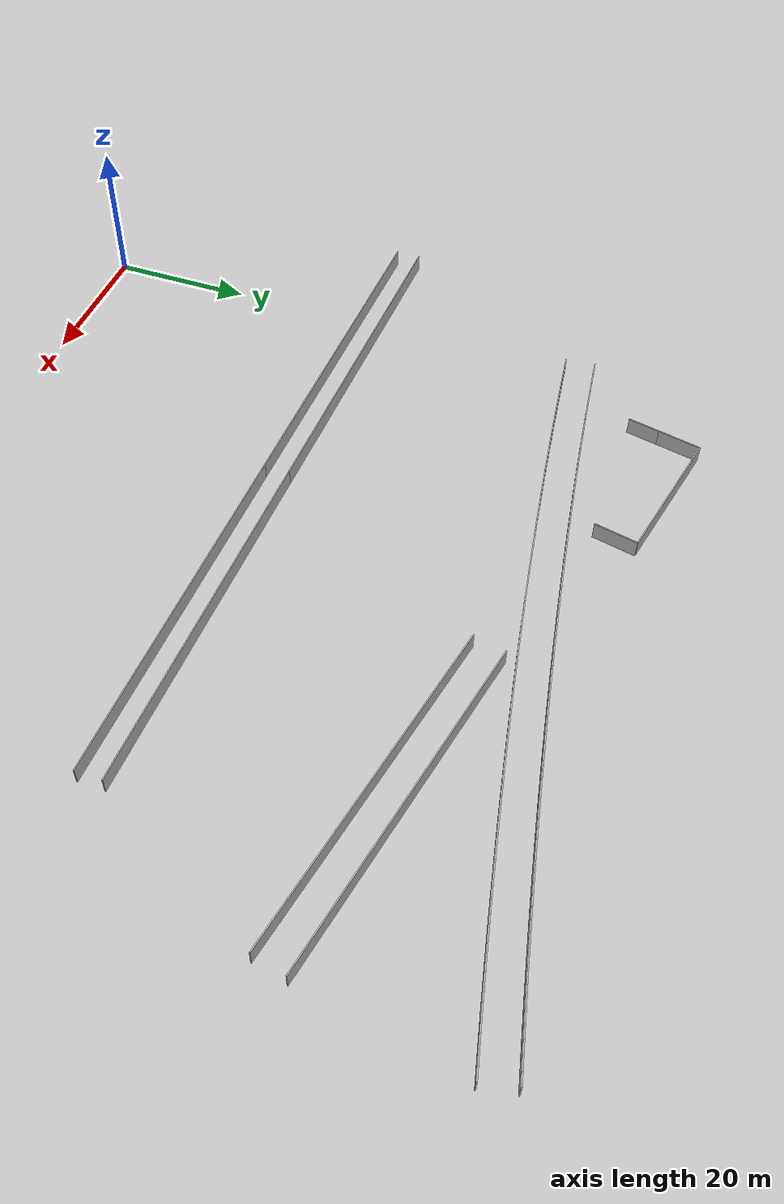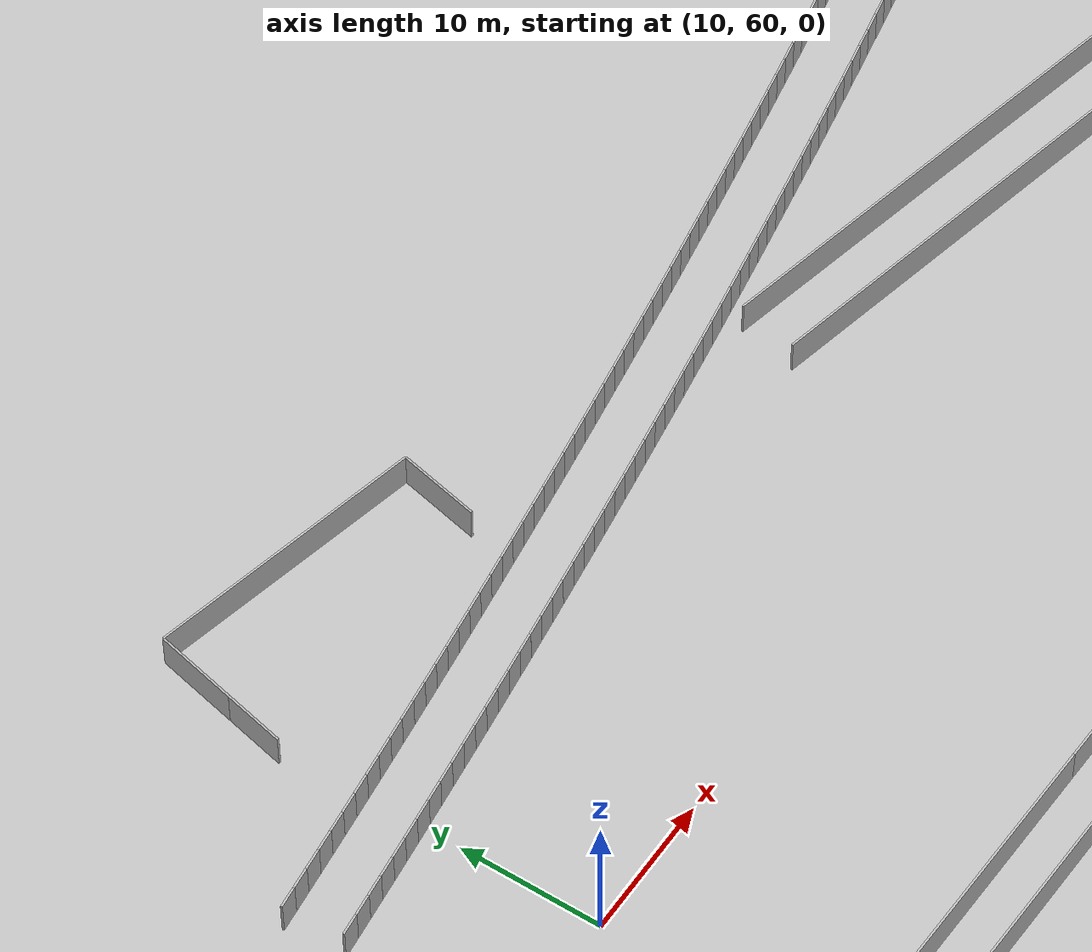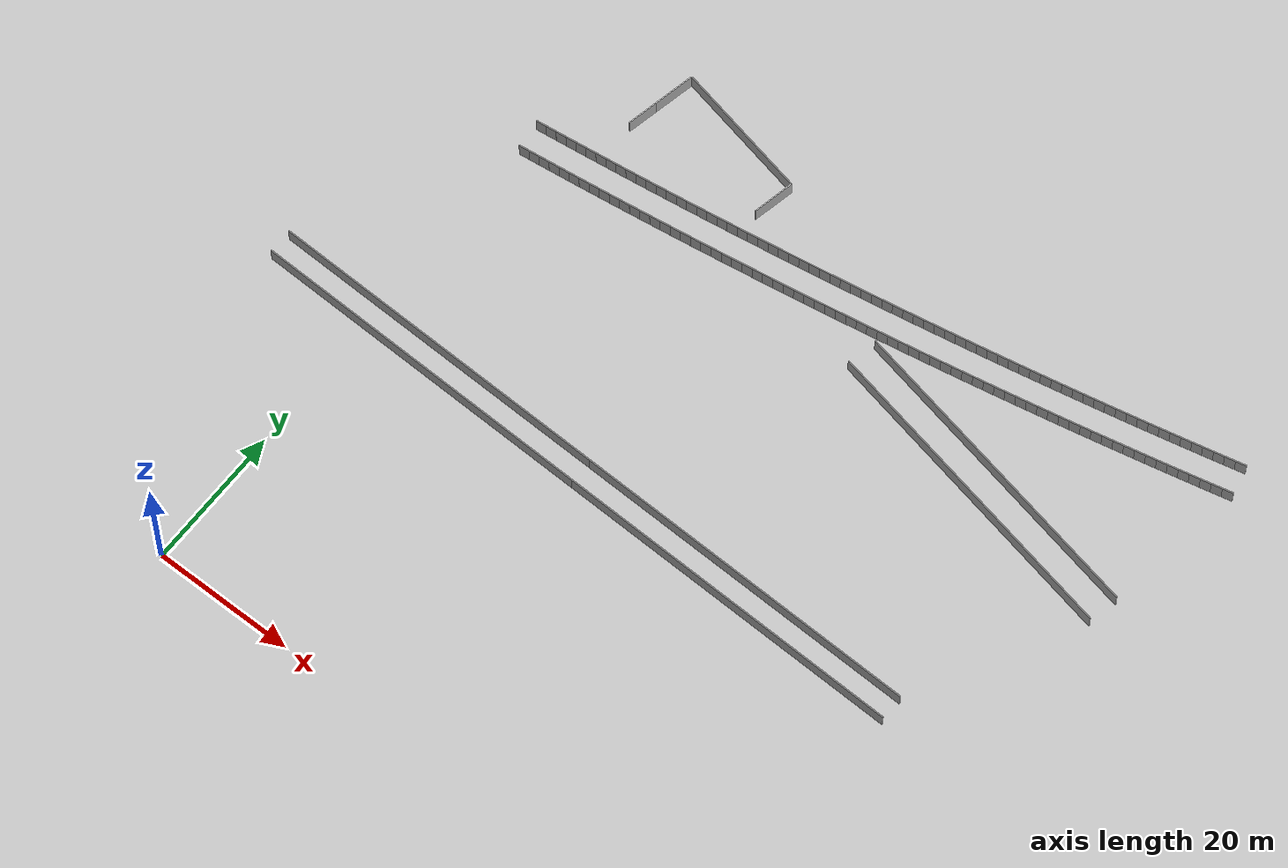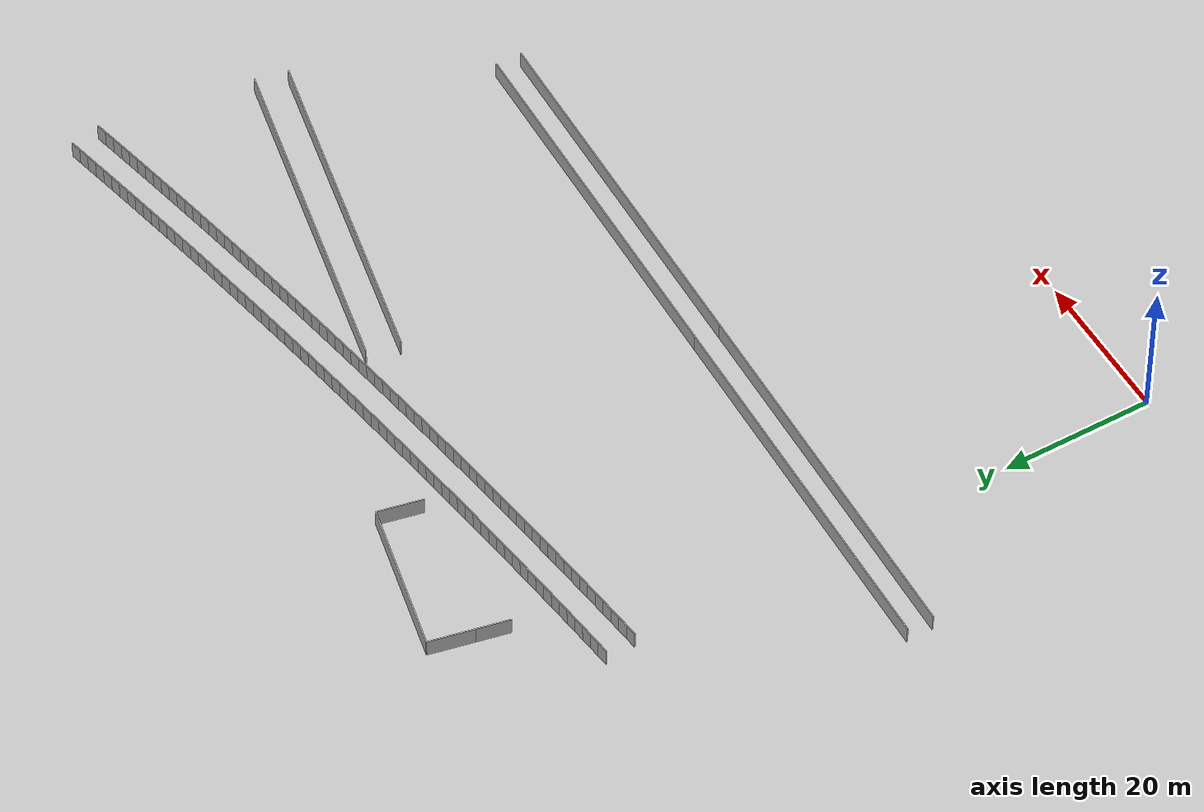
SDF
<?xml version="1.0" ?>
<sdf version="1.6">
  <model name="sps_1401">
    <pose frame="">0 0 0 0 -0 0</pose>
    <static>1</static>
    <self_collide>0</self_collide>
    <allow_auto_disable>0</allow_auto_disable>
    <link name="Wall137">
      <kinematic>0</kinematic>
      <gravity>1</gravity>
      <self_collide>0</self_collide>
      <collision name="collision">
        <geometry>
          <box>
            <size>20 0.15 2.5</size>
          </box>
        </geometry>
        <pose frame="">0 0 0 0 -0 0</pose>
      </collision>
      <visual name="visual">
        <geometry>
          <box>
            <size>20 0.15 2.5</size>
          </box>
        </geometry>
        <pose frame="">0 0 0 0 -0 0</pose>
        <cast_shadows>1</cast_shadows>
        <transparency>0.0</transparency>
      </visual>
      <pose frame="">21.0121 90.5186 1.25 0 0 -0.214245</pose>
    </link>
    <link name="Wall240">
      <kinematic>0</kinematic>
      <gravity>1</gravity>
      <self_collide>0</self_collide>
      <collision name="collision">
        <geometry>
          <box>
            <size>5.9893 0.15 2.5</size>
          </box>
        </geometry>
        <pose frame="">0 0 0 0 -0 0</pose>
      </collision>
      <visual name="visual">
        <geometry>
          <box>
            <size>5.9893 0.15 2.5</size>
          </box>
        </geometry>
        <pose frame="">0 0 0 0 -0 0</pose>
        <cast_shadows>1</cast_shadows>
        <transparency>0.0</transparency>
      </visual>
      <pose frame="">30.1468 85.4663 1.25 0 0 -1.78505</pose>
    </link>
    <link name="Wall374">
      <kinematic>0</kinematic>
      <gravity>1</gravity>
      <self_collide>0</self_collide>
      <collision name="collision">
        <geometry>
          <box>
            <size>5.9893 0.15 2.5</size>
          </box>
        </geometry>
        <pose frame="">0 0 0 0 -0 0</pose>
      </collision>
      <visual name="visual">
        <geometry>
          <box>
            <size>5.9893 0.15 2.5</size>
          </box>
        </geometry>
        <pose frame="">0 0 0 0 -0 0</pose>
        <cast_shadows>1</cast_shadows>
        <transparency>0.0</transparency>
      </visual>
      <pose frame="">10.604 89.7185 1.25 0 0 -1.78505</pose>
    </link>
    <link name="Wall459">
      <kinematic>0</kinematic>
      <gravity>1</gravity>
      <self_collide>0</self_collide>
      <collision name="collision">
        <geometry>
          <box>
            <size>50.0165 0.15 2.5</size>
          </box>
        </geometry>
        <pose frame="">0 0 0 0 -0 0</pose>
      </collision>
      <visual name="visual">
        <geometry>
          <box>
            <size>50.0165 0.15 2.5</size>
          </box>
        </geometry>
        <pose frame="">0 0 0 0 -0 0</pose>
        <cast_shadows>1</cast_shadows>
        <transparency>0.0</transparency>
      </visual>
      <pose frame="">59.4694 38.2343 1.25 0 -0 3.11591</pose>
    </link>
    <link name="Wall460">
      <kinematic>0</kinematic>
      <gravity>1</gravity>
      <self_collide>0</self_collide>
      <collision name="collision">
        <geometry>
          <box>
            <size>50.0165 0.15 2.5</size>
          </box>
        </geometry>
        <pose frame="">0 0 0 0 -0 0</pose>
      </collision>
      <visual name="visual">
        <geometry>
          <box>
            <size>50.0165 0.15 2.5</size>
          </box>
        </geometry>
        <pose frame="">0 0 0 0 -0 0</pose>
        <cast_shadows>1</cast_shadows>
        <transparency>0.0</transparency>
      </visual>
      <pose frame="">9.46944 39.5186 1.25 0 -0 3.11591</pose>
    </link>
    <link name="Wall465">
      <kinematic>0</kinematic>
      <gravity>1</gravity>
      <self_collide>0</self_collide>
      <collision name="collision">
        <geometry>
          <box>
            <size>50.0165 0.15 2.5</size>
          </box>
        </geometry>
        <pose frame="">0 0 0 0 -0 0</pose>
      </collision>
      <visual name="visual">
        <geometry>
          <box>
            <size>50.0165 0.15 2.5</size>
          </box>
        </geometry>
        <pose frame="">0 0 0 0 -0 0</pose>
        <cast_shadows>1</cast_shadows>
        <transparency>0.0</transparency>
      </visual>
      <pose frame="">9.46944 43.0195 1.25 0 0 -0.0256802</pose>
    </link>
    <link name="Wall466">
      <kinematic>0</kinematic>
      <gravity>1</gravity>
      <self_collide>0</self_collide>
      <collision name="collision">
        <geometry>
          <box>
            <size>50.0165 0.15 2.5</size>
          </box>
        </geometry>
        <pose frame="">0 0 0 0 -0 0</pose>
      </collision>
      <visual name="visual">
        <geometry>
          <box>
            <size>50.0165 0.15 2.5</size>
          </box>
        </geometry>
        <pose frame="">0 0 0 0 -0 0</pose>
        <cast_shadows>1</cast_shadows>
        <transparency>0.0</transparency>
      </visual>
      <pose frame="">59.4694 41.7352 1.25 0 0 -0.0256802</pose>
    </link>
    <link name="Wall2702">
      <kinematic>0</kinematic>
      <gravity>1</gravity>
      <self_collide>0</self_collide>
      <collision name="collision">
        <geometry>
          <box>
            <size>4.39977 0.15 2.5</size>
          </box>
        </geometry>
        <pose frame="">0 0 0 0 -0 0</pose>
      </collision>
      <visual name="visual">
        <geometry>
          <box>
            <size>4.39977 0.15 2.5</size>
          </box>
        </geometry>
        <pose frame="">0 0 0 0 -0 0</pose>
        <cast_shadows>1</cast_shadows>
        <transparency>0.0</transparency>
      </visual>
      <pose frame="">9.49975 84.6427 1.25 0 0 -1.78502</pose>
    </link>
    <link name="Wall3621">
      <kinematic>0</kinematic>
      <gravity>1</gravity>
      <self_collide>0</self_collide>
      <collision name="collision">
        <geometry>
          <box>
            <size>45.9351 0.15 2.5</size>
          </box>
        </geometry>
        <pose frame="">0 0 0 0 -0 0</pose>
      </collision>
      <visual name="visual">
        <geometry>
          <box>
            <size>45.9351 0.15 2.5</size>
          </box>
        </geometry>
        <pose frame="">0 0 0 0 -0 0</pose>
        <cast_shadows>1</cast_shadows>
        <transparency>0.0</transparency>
      </visual>
      <pose frame="">74.1661 68.5489 1.25 0 -0 2.93706</pose>
    </link>
    <link name="Wall3778">
      <kinematic>0</kinematic>
      <gravity>1</gravity>
      <self_collide>0</self_collide>
      <collision name="collision">
        <geometry>
          <box>
            <size>1.49654 0.15 2.5</size>
          </box>
        </geometry>
        <pose frame="">0 0 0 0 -0 0</pose>
      </collision>
      <visual name="visual">
        <geometry>
          <box>
            <size>1.49654 0.15 2.5</size>
          </box>
        </geometry>
        <pose frame="">0 0 0 0 -0 0</pose>
        <cast_shadows>1</cast_shadows>
        <transparency>0.0</transparency>
      </visual>
      <pose frame="">0.206657 75.4595 1.25 0 -0 0.116539</pose>
    </link>
    <link name="Wall3779">
      <kinematic>0</kinematic>
      <gravity>1</gravity>
      <self_collide>0</self_collide>
      <collision name="collision">
        <geometry>
          <box>
            <size>1.49646 0.15 2.5</size>
          </box>
        </geometry>
        <pose frame="">0 0 0 0 -0 0</pose>
      </collision>
      <visual name="visual">
        <geometry>
          <box>
            <size>1.49646 0.15 2.5</size>
          </box>
        </geometry>
        <pose frame="">0 0 0 0 -0 0</pose>
        <cast_shadows>1</cast_shadows>
        <transparency>0.0</transparency>
      </visual>
      <pose frame="">1.69286 75.6347 1.25 0 -0 0.118148</pose>
    </link>
    <link name="Wall3780">
      <kinematic>0</kinematic>
      <gravity>1</gravity>
      <self_collide>0</self_collide>
      <collision name="collision">
        <geometry>
          <box>
            <size>1.49652 0.15 2.5</size>
          </box>
        </geometry>
        <pose frame="">0 0 0 0 -0 0</pose>
      </collision>
      <visual name="visual">
        <geometry>
          <box>
            <size>1.49652 0.15 2.5</size>
          </box>
        </geometry>
        <pose frame="">0 0 0 0 -0 0</pose>
        <cast_shadows>1</cast_shadows>
        <transparency>0.0</transparency>
      </visual>
      <pose frame="">3.17876 75.8124 1.25 0 -0 0.119868</pose>
    </link>
    <link name="Wall3781">
      <kinematic>0</kinematic>
      <gravity>1</gravity>
      <self_collide>0</self_collide>
      <collision name="collision">
        <geometry>
          <box>
            <size>1.4964 0.15 2.5</size>
          </box>
        </geometry>
        <pose frame="">0 0 0 0 -0 0</pose>
      </collision>
      <visual name="visual">
        <geometry>
          <box>
            <size>1.4964 0.15 2.5</size>
          </box>
        </geometry>
        <pose frame="">0 0 0 0 -0 0</pose>
        <cast_shadows>1</cast_shadows>
        <transparency>0.0</transparency>
      </visual>
      <pose frame="">4.66436 75.9924 1.25 0 -0 0.121274</pose>
    </link>
    <link name="Wall3782">
      <kinematic>0</kinematic>
      <gravity>1</gravity>
      <self_collide>0</self_collide>
      <collision name="collision">
        <geometry>
          <box>
            <size>1.49645 0.15 2.5</size>
          </box>
        </geometry>
        <pose frame="">0 0 0 0 -0 0</pose>
      </collision>
      <visual name="visual">
        <geometry>
          <box>
            <size>1.49645 0.15 2.5</size>
          </box>
        </geometry>
        <pose frame="">0 0 0 0 -0 0</pose>
        <cast_shadows>1</cast_shadows>
        <transparency>0.0</transparency>
      </visual>
      <pose frame="">6.14965 76.1746 1.25 0 -0 0.122873</pose>
    </link>
    <link name="Wall3783">
      <kinematic>0</kinematic>
      <gravity>1</gravity>
      <self_collide>0</self_collide>
      <collision name="collision">
        <geometry>
          <box>
            <size>1.4964 0.15 2.5</size>
          </box>
        </geometry>
        <pose frame="">0 0 0 0 -0 0</pose>
      </collision>
      <visual name="visual">
        <geometry>
          <box>
            <size>1.4964 0.15 2.5</size>
          </box>
        </geometry>
        <pose frame="">0 0 0 0 -0 0</pose>
        <cast_shadows>1</cast_shadows>
        <transparency>0.0</transparency>
      </visual>
      <pose frame="">7.63464 76.3593 1.25 0 -0 0.124603</pose>
    </link>
    <link name="Wall3784">
      <kinematic>0</kinematic>
      <gravity>1</gravity>
      <self_collide>0</self_collide>
      <collision name="collision">
        <geometry>
          <box>
            <size>1.49666 0.15 2.5</size>
          </box>
        </geometry>
        <pose frame="">0 0 0 0 -0 0</pose>
      </collision>
      <visual name="visual">
        <geometry>
          <box>
            <size>1.49666 0.15 2.5</size>
          </box>
        </geometry>
        <pose frame="">0 0 0 0 -0 0</pose>
        <cast_shadows>1</cast_shadows>
        <transparency>0.0</transparency>
      </visual>
      <pose frame="">9.11944 76.5463 1.25 0 -0 0.125938</pose>
    </link>
    <link name="Wall3785">
      <kinematic>0</kinematic>
      <gravity>1</gravity>
      <self_collide>0</self_collide>
      <collision name="collision">
        <geometry>
          <box>
            <size>1.49662 0.15 2.5</size>
          </box>
        </geometry>
        <pose frame="">0 0 0 0 -0 0</pose>
      </collision>
      <visual name="visual">
        <geometry>
          <box>
            <size>1.49662 0.15 2.5</size>
          </box>
        </geometry>
        <pose frame="">0 0 0 0 -0 0</pose>
        <cast_shadows>1</cast_shadows>
        <transparency>0.0</transparency>
      </visual>
      <pose frame="">10.6041 76.7356 1.25 0 -0 0.127709</pose>
    </link>
    <link name="Wall3786">
      <kinematic>0</kinematic>
      <gravity>1</gravity>
      <self_collide>0</self_collide>
      <collision name="collision">
        <geometry>
          <box>
            <size>1.49651 0.15 2.5</size>
          </box>
        </geometry>
        <pose frame="">0 0 0 0 -0 0</pose>
      </collision>
      <visual name="visual">
        <geometry>
          <box>
            <size>1.49651 0.15 2.5</size>
          </box>
        </geometry>
        <pose frame="">0 0 0 0 -0 0</pose>
        <cast_shadows>1</cast_shadows>
        <transparency>0.0</transparency>
      </visual>
      <pose frame="">12.0883 76.9274 1.25 0 -0 0.129323</pose>
    </link>
    <link name="Wall3787">
      <kinematic>0</kinematic>
      <gravity>1</gravity>
      <self_collide>0</self_collide>
      <collision name="collision">
        <geometry>
          <box>
            <size>1.49655 0.15 2.5</size>
          </box>
        </geometry>
        <pose frame="">0 0 0 0 -0 0</pose>
      </collision>
      <visual name="visual">
        <geometry>
          <box>
            <size>1.49655 0.15 2.5</size>
          </box>
        </geometry>
        <pose frame="">0 0 0 0 -0 0</pose>
        <cast_shadows>1</cast_shadows>
        <transparency>0.0</transparency>
      </visual>
      <pose frame="">13.5722 77.1215 1.25 0 -0 0.1308</pose>
    </link>
    <link name="Wall3788">
      <kinematic>0</kinematic>
      <gravity>1</gravity>
      <self_collide>0</self_collide>
      <collision name="collision">
        <geometry>
          <box>
            <size>1.49651 0.15 2.5</size>
          </box>
        </geometry>
        <pose frame="">0 0 0 0 -0 0</pose>
      </collision>
      <visual name="visual">
        <geometry>
          <box>
            <size>1.49651 0.15 2.5</size>
          </box>
        </geometry>
        <pose frame="">0 0 0 0 -0 0</pose>
        <cast_shadows>1</cast_shadows>
        <transparency>0.0</transparency>
      </visual>
      <pose frame="">15.0557 77.3179 1.25 0 -0 0.132449</pose>
    </link>
    <link name="Wall3789">
      <kinematic>0</kinematic>
      <gravity>1</gravity>
      <self_collide>0</self_collide>
      <collision name="collision">
        <geometry>
          <box>
            <size>1.49664 0.15 2.5</size>
          </box>
        </geometry>
        <pose frame="">0 0 0 0 -0 0</pose>
      </collision>
      <visual name="visual">
        <geometry>
          <box>
            <size>1.49664 0.15 2.5</size>
          </box>
        </geometry>
        <pose frame="">0 0 0 0 -0 0</pose>
        <cast_shadows>1</cast_shadows>
        <transparency>0.0</transparency>
      </visual>
      <pose frame="">16.5391 77.5167 1.25 0 -0 0.134042</pose>
    </link>
    <link name="Wall3790">
      <kinematic>0</kinematic>
      <gravity>1</gravity>
      <self_collide>0</self_collide>
      <collision name="collision">
        <geometry>
          <box>
            <size>1.49651 0.15 2.5</size>
          </box>
        </geometry>
        <pose frame="">0 0 0 0 -0 0</pose>
      </collision>
      <visual name="visual">
        <geometry>
          <box>
            <size>1.49651 0.15 2.5</size>
          </box>
        </geometry>
        <pose frame="">0 0 0 0 -0 0</pose>
        <cast_shadows>1</cast_shadows>
        <transparency>0.0</transparency>
      </visual>
      <pose frame="">18.0221 77.7178 1.25 0 -0 0.135535</pose>
    </link>
    <link name="Wall3791">
      <kinematic>0</kinematic>
      <gravity>1</gravity>
      <self_collide>0</self_collide>
      <collision name="collision">
        <geometry>
          <box>
            <size>1.4965 0.15 2.5</size>
          </box>
        </geometry>
        <pose frame="">0 0 0 0 -0 0</pose>
      </collision>
      <visual name="visual">
        <geometry>
          <box>
            <size>1.4965 0.15 2.5</size>
          </box>
        </geometry>
        <pose frame="">0 0 0 0 -0 0</pose>
        <cast_shadows>1</cast_shadows>
        <transparency>0.0</transparency>
      </visual>
      <pose frame="">19.5047 77.9213 1.25 0 -0 0.137265</pose>
    </link>
    <link name="Wall3792">
      <kinematic>0</kinematic>
      <gravity>1</gravity>
      <self_collide>0</self_collide>
      <collision name="collision">
        <geometry>
          <box>
            <size>1.49656 0.15 2.5</size>
          </box>
        </geometry>
        <pose frame="">0 0 0 0 -0 0</pose>
      </collision>
      <visual name="visual">
        <geometry>
          <box>
            <size>1.49656 0.15 2.5</size>
          </box>
        </geometry>
        <pose frame="">0 0 0 0 -0 0</pose>
        <cast_shadows>1</cast_shadows>
        <transparency>0.0</transparency>
      </visual>
      <pose frame="">20.987 78.1272 1.25 0 -0 0.138742</pose>
    </link>
    <link name="Wall3793">
      <kinematic>0</kinematic>
      <gravity>1</gravity>
      <self_collide>0</self_collide>
      <collision name="collision">
        <geometry>
          <box>
            <size>1.49654 0.15 2.5</size>
          </box>
        </geometry>
        <pose frame="">0 0 0 0 -0 0</pose>
      </collision>
      <visual name="visual">
        <geometry>
          <box>
            <size>1.49654 0.15 2.5</size>
          </box>
        </geometry>
        <pose frame="">0 0 0 0 -0 0</pose>
        <cast_shadows>1</cast_shadows>
        <transparency>0.0</transparency>
      </visual>
      <pose frame="">22.469 78.3354 1.25 0 -0 0.140392</pose>
    </link>
    <link name="Wall3794">
      <kinematic>0</kinematic>
      <gravity>1</gravity>
      <self_collide>0</self_collide>
      <collision name="collision">
        <geometry>
          <box>
            <size>1.49642 0.15 2.5</size>
          </box>
        </geometry>
        <pose frame="">0 0 0 0 -0 0</pose>
      </collision>
      <visual name="visual">
        <geometry>
          <box>
            <size>1.49642 0.15 2.5</size>
          </box>
        </geometry>
        <pose frame="">0 0 0 0 -0 0</pose>
        <cast_shadows>1</cast_shadows>
        <transparency>0.0</transparency>
      </visual>
      <pose frame="">23.9506 78.5459 1.25 0 -0 0.141886</pose>
    </link>
    <link name="Wall3795">
      <kinematic>0</kinematic>
      <gravity>1</gravity>
      <self_collide>0</self_collide>
      <collision name="collision">
        <geometry>
          <box>
            <size>1.49658 0.15 2.5</size>
          </box>
        </geometry>
        <pose frame="">0 0 0 0 -0 0</pose>
      </collision>
      <visual name="visual">
        <geometry>
          <box>
            <size>1.49658 0.15 2.5</size>
          </box>
        </geometry>
        <pose frame="">0 0 0 0 -0 0</pose>
        <cast_shadows>1</cast_shadows>
        <transparency>0.0</transparency>
      </visual>
      <pose frame="">25.4318 78.7587 1.25 0 -0 0.143477</pose>
    </link>
    <link name="Wall3796">
      <kinematic>0</kinematic>
      <gravity>1</gravity>
      <self_collide>0</self_collide>
      <collision name="collision">
        <geometry>
          <box>
            <size>1.49659 0.15 2.5</size>
          </box>
        </geometry>
        <pose frame="">0 0 0 0 -0 0</pose>
      </collision>
      <visual name="visual">
        <geometry>
          <box>
            <size>1.49659 0.15 2.5</size>
          </box>
        </geometry>
        <pose frame="">0 0 0 0 -0 0</pose>
        <cast_shadows>1</cast_shadows>
        <transparency>0.0</transparency>
      </visual>
      <pose frame="">26.9129 78.974 1.25 0 -0 0.145248</pose>
    </link>
    <link name="Wall3797">
      <kinematic>0</kinematic>
      <gravity>1</gravity>
      <self_collide>0</self_collide>
      <collision name="collision">
        <geometry>
          <box>
            <size>1.49665 0.15 2.5</size>
          </box>
        </geometry>
        <pose frame="">0 0 0 0 -0 0</pose>
      </collision>
      <visual name="visual">
        <geometry>
          <box>
            <size>1.49665 0.15 2.5</size>
          </box>
        </geometry>
        <pose frame="">0 0 0 0 -0 0</pose>
        <cast_shadows>1</cast_shadows>
        <transparency>0.0</transparency>
      </visual>
      <pose frame="">28.3936 79.1916 1.25 0 -0 0.146603</pose>
    </link>
    <link name="Wall3798">
      <kinematic>0</kinematic>
      <gravity>1</gravity>
      <self_collide>0</self_collide>
      <collision name="collision">
        <geometry>
          <box>
            <size>1.4966 0.15 2.5</size>
          </box>
        </geometry>
        <pose frame="">0 0 0 0 -0 0</pose>
      </collision>
      <visual name="visual">
        <geometry>
          <box>
            <size>1.4966 0.15 2.5</size>
          </box>
        </geometry>
        <pose frame="">0 0 0 0 -0 0</pose>
        <cast_shadows>1</cast_shadows>
        <transparency>0.0</transparency>
      </visual>
      <pose frame="">29.874 79.4115 1.25 0 -0 0.148339</pose>
    </link>
    <link name="Wall3799">
      <kinematic>0</kinematic>
      <gravity>1</gravity>
      <self_collide>0</self_collide>
      <collision name="collision">
        <geometry>
          <box>
            <size>1.49638 0.15 2.5</size>
          </box>
        </geometry>
        <pose frame="">0 0 0 0 -0 0</pose>
      </collision>
      <visual name="visual">
        <geometry>
          <box>
            <size>1.49638 0.15 2.5</size>
          </box>
        </geometry>
        <pose frame="">0 0 0 0 -0 0</pose>
        <cast_shadows>1</cast_shadows>
        <transparency>0.0</transparency>
      </visual>
      <pose frame="">31.3538 79.6338 1.25 0 -0 0.149846</pose>
    </link>
    <link name="Wall3800">
      <kinematic>0</kinematic>
      <gravity>1</gravity>
      <self_collide>0</self_collide>
      <collision name="collision">
        <geometry>
          <box>
            <size>1.49656 0.15 2.5</size>
          </box>
        </geometry>
        <pose frame="">0 0 0 0 -0 0</pose>
      </collision>
      <visual name="visual">
        <geometry>
          <box>
            <size>1.49656 0.15 2.5</size>
          </box>
        </geometry>
        <pose frame="">0 0 0 0 -0 0</pose>
        <cast_shadows>1</cast_shadows>
        <transparency>0.0</transparency>
      </visual>
      <pose frame="">32.8334 79.8584 1.25 0 -0 0.151437</pose>
    </link>
    <link name="Wall3801">
      <kinematic>0</kinematic>
      <gravity>1</gravity>
      <self_collide>0</self_collide>
      <collision name="collision">
        <geometry>
          <box>
            <size>1.49651 0.15 2.5</size>
          </box>
        </geometry>
        <pose frame="">0 0 0 0 -0 0</pose>
      </collision>
      <visual name="visual">
        <geometry>
          <box>
            <size>1.49651 0.15 2.5</size>
          </box>
        </geometry>
        <pose frame="">0 0 0 0 -0 0</pose>
        <cast_shadows>1</cast_shadows>
        <transparency>0.0</transparency>
      </visual>
      <pose frame="">34.3126 80.0854 1.25 0 -0 0.153093</pose>
    </link>
    <link name="Wall3802">
      <kinematic>0</kinematic>
      <gravity>1</gravity>
      <self_collide>0</self_collide>
      <collision name="collision">
        <geometry>
          <box>
            <size>1.49642 0.15 2.5</size>
          </box>
        </geometry>
        <pose frame="">0 0 0 0 -0 0</pose>
      </collision>
      <visual name="visual">
        <geometry>
          <box>
            <size>1.49642 0.15 2.5</size>
          </box>
        </geometry>
        <pose frame="">0 0 0 0 -0 0</pose>
        <cast_shadows>1</cast_shadows>
        <transparency>0.0</transparency>
      </visual>
      <pose frame="">35.7914 80.3147 1.25 0 -0 0.154587</pose>
    </link>
    <link name="Wall3803">
      <kinematic>0</kinematic>
      <gravity>1</gravity>
      <self_collide>0</self_collide>
      <collision name="collision">
        <geometry>
          <box>
            <size>1.49661 0.15 2.5</size>
          </box>
        </geometry>
        <pose frame="">0 0 0 0 -0 0</pose>
      </collision>
      <visual name="visual">
        <geometry>
          <box>
            <size>1.49661 0.15 2.5</size>
          </box>
        </geometry>
        <pose frame="">0 0 0 0 -0 0</pose>
        <cast_shadows>1</cast_shadows>
        <transparency>0.0</transparency>
      </visual>
      <pose frame="">37.2699 80.5463 1.25 0 -0 0.156178</pose>
    </link>
    <link name="Wall3804">
      <kinematic>0</kinematic>
      <gravity>1</gravity>
      <self_collide>0</self_collide>
      <collision name="collision">
        <geometry>
          <box>
            <size>1.4966 0.15 2.5</size>
          </box>
        </geometry>
        <pose frame="">0 0 0 0 -0 0</pose>
      </collision>
      <visual name="visual">
        <geometry>
          <box>
            <size>1.4966 0.15 2.5</size>
          </box>
        </geometry>
        <pose frame="">0 0 0 0 -0 0</pose>
        <cast_shadows>1</cast_shadows>
        <transparency>0.0</transparency>
      </visual>
      <pose frame="">38.7481 80.7802 1.25 0 -0 0.157706</pose>
    </link>
    <link name="Wall3805">
      <kinematic>0</kinematic>
      <gravity>1</gravity>
      <self_collide>0</self_collide>
      <collision name="collision">
        <geometry>
          <box>
            <size>1.49657 0.15 2.5</size>
          </box>
        </geometry>
        <pose frame="">0 0 0 0 -0 0</pose>
      </collision>
      <visual name="visual">
        <geometry>
          <box>
            <size>1.49657 0.15 2.5</size>
          </box>
        </geometry>
        <pose frame="">0 0 0 0 -0 0</pose>
        <cast_shadows>1</cast_shadows>
        <transparency>0.0</transparency>
      </visual>
      <pose frame="">40.2259 81.0165 1.25 0 -0 0.159403</pose>
    </link>
    <link name="Wall3806">
      <kinematic>0</kinematic>
      <gravity>1</gravity>
      <self_collide>0</self_collide>
      <collision name="collision">
        <geometry>
          <box>
            <size>1.49651 0.15 2.5</size>
          </box>
        </geometry>
        <pose frame="">0 0 0 0 -0 0</pose>
      </collision>
      <visual name="visual">
        <geometry>
          <box>
            <size>1.49651 0.15 2.5</size>
          </box>
        </geometry>
        <pose frame="">0 0 0 0 -0 0</pose>
        <cast_shadows>1</cast_shadows>
        <transparency>0.0</transparency>
      </visual>
      <pose frame="">41.7033 81.2552 1.25 0 -0 0.160938</pose>
    </link>
    <link name="Wall3807">
      <kinematic>0</kinematic>
      <gravity>1</gravity>
      <self_collide>0</self_collide>
      <collision name="collision">
        <geometry>
          <box>
            <size>1.49653 0.15 2.5</size>
          </box>
        </geometry>
        <pose frame="">0 0 0 0 -0 0</pose>
      </collision>
      <visual name="visual">
        <geometry>
          <box>
            <size>1.49653 0.15 2.5</size>
          </box>
        </geometry>
        <pose frame="">0 0 0 0 -0 0</pose>
        <cast_shadows>1</cast_shadows>
        <transparency>0.0</transparency>
      </visual>
      <pose frame="">43.1803 81.4962 1.25 0 -0 0.162547</pose>
    </link>
    <link name="Wall3808">
      <kinematic>0</kinematic>
      <gravity>1</gravity>
      <self_collide>0</self_collide>
      <collision name="collision">
        <geometry>
          <box>
            <size>1.49648 0.15 2.5</size>
          </box>
        </geometry>
        <pose frame="">0 0 0 0 -0 0</pose>
      </collision>
      <visual name="visual">
        <geometry>
          <box>
            <size>1.49648 0.15 2.5</size>
          </box>
        </geometry>
        <pose frame="">0 0 0 0 -0 0</pose>
        <cast_shadows>1</cast_shadows>
        <transparency>0.0</transparency>
      </visual>
      <pose frame="">44.6569 81.7395 1.25 0 -0 0.164083</pose>
    </link>
    <link name="Wall3809">
      <kinematic>0</kinematic>
      <gravity>1</gravity>
      <self_collide>0</self_collide>
      <collision name="collision">
        <geometry>
          <box>
            <size>1.4965 0.15 2.5</size>
          </box>
        </geometry>
        <pose frame="">0 0 0 0 -0 0</pose>
      </collision>
      <visual name="visual">
        <geometry>
          <box>
            <size>1.4965 0.15 2.5</size>
          </box>
        </geometry>
        <pose frame="">0 0 0 0 -0 0</pose>
        <cast_shadows>1</cast_shadows>
        <transparency>0.0</transparency>
      </visual>
      <pose frame="">46.133 81.9851 1.25 0 -0 0.165652</pose>
    </link>
    <link name="Wall3810">
      <kinematic>0</kinematic>
      <gravity>1</gravity>
      <self_collide>0</self_collide>
      <collision name="collision">
        <geometry>
          <box>
            <size>1.49648 0.15 2.5</size>
          </box>
        </geometry>
        <pose frame="">0 0 0 0 -0 0</pose>
      </collision>
      <visual name="visual">
        <geometry>
          <box>
            <size>1.49648 0.15 2.5</size>
          </box>
        </geometry>
        <pose frame="">0 0 0 0 -0 0</pose>
        <cast_shadows>1</cast_shadows>
        <transparency>0.0</transparency>
      </visual>
      <pose frame="">47.6088 82.2331 1.25 0 -0 0.167308</pose>
    </link>
    <link name="Wall3811">
      <kinematic>0</kinematic>
      <gravity>1</gravity>
      <self_collide>0</self_collide>
      <collision name="collision">
        <geometry>
          <box>
            <size>1.49652 0.15 2.5</size>
          </box>
        </geometry>
        <pose frame="">0 0 0 0 -0 0</pose>
      </collision>
      <visual name="visual">
        <geometry>
          <box>
            <size>1.49652 0.15 2.5</size>
          </box>
        </geometry>
        <pose frame="">0 0 0 0 -0 0</pose>
        <cast_shadows>1</cast_shadows>
        <transparency>0.0</transparency>
      </visual>
      <pose frame="">49.0843 82.4835 1.25 0 -0 0.168917</pose>
    </link>
    <link name="Wall3812">
      <kinematic>0</kinematic>
      <gravity>1</gravity>
      <self_collide>0</self_collide>
      <collision name="collision">
        <geometry>
          <box>
            <size>1.49666 0.15 2.5</size>
          </box>
        </geometry>
        <pose frame="">0 0 0 0 -0 0</pose>
      </collision>
      <visual name="visual">
        <geometry>
          <box>
            <size>1.49666 0.15 2.5</size>
          </box>
        </geometry>
        <pose frame="">0 0 0 0 -0 0</pose>
        <cast_shadows>1</cast_shadows>
        <transparency>0.0</transparency>
      </visual>
      <pose frame="">50.5593 82.7362 1.25 0 -0 0.170432</pose>
    </link>
    <link name="Wall3813">
      <kinematic>0</kinematic>
      <gravity>1</gravity>
      <self_collide>0</self_collide>
      <collision name="collision">
        <geometry>
          <box>
            <size>1.49651 0.15 2.5</size>
          </box>
        </geometry>
        <pose frame="">0 0 0 0 -0 0</pose>
      </collision>
      <visual name="visual">
        <geometry>
          <box>
            <size>1.49651 0.15 2.5</size>
          </box>
        </geometry>
        <pose frame="">0 0 0 0 -0 0</pose>
        <cast_shadows>1</cast_shadows>
        <transparency>0.0</transparency>
      </visual>
      <pose frame="">52.034 82.9912 1.25 0 -0 0.172021</pose>
    </link>
    <link name="Wall3814">
      <kinematic>0</kinematic>
      <gravity>1</gravity>
      <self_collide>0</self_collide>
      <collision name="collision">
        <geometry>
          <box>
            <size>1.49651 0.15 2.5</size>
          </box>
        </geometry>
        <pose frame="">0 0 0 0 -0 0</pose>
      </collision>
      <visual name="visual">
        <geometry>
          <box>
            <size>1.49651 0.15 2.5</size>
          </box>
        </geometry>
        <pose frame="">0 0 0 0 -0 0</pose>
        <cast_shadows>1</cast_shadows>
        <transparency>0.0</transparency>
      </visual>
      <pose frame="">53.5083 83.2486 1.25 0 -0 0.173678</pose>
    </link>
    <link name="Wall3815">
      <kinematic>0</kinematic>
      <gravity>1</gravity>
      <self_collide>0</self_collide>
      <collision name="collision">
        <geometry>
          <box>
            <size>1.49647 0.15 2.5</size>
          </box>
        </geometry>
        <pose frame="">0 0 0 0 -0 0</pose>
      </collision>
      <visual name="visual">
        <geometry>
          <box>
            <size>1.49647 0.15 2.5</size>
          </box>
        </geometry>
        <pose frame="">0 0 0 0 -0 0</pose>
        <cast_shadows>1</cast_shadows>
        <transparency>0.0</transparency>
      </visual>
      <pose frame="">54.982 83.5083 1.25 0 -0 0.175173</pose>
    </link>
    <link name="Wall3816">
      <kinematic>0</kinematic>
      <gravity>1</gravity>
      <self_collide>0</self_collide>
      <collision name="collision">
        <geometry>
          <box>
            <size>1.49635 0.15 2.5</size>
          </box>
        </geometry>
        <pose frame="">0 0 0 0 -0 0</pose>
      </collision>
      <visual name="visual">
        <geometry>
          <box>
            <size>1.49635 0.15 2.5</size>
          </box>
        </geometry>
        <pose frame="">0 0 0 0 -0 0</pose>
        <cast_shadows>1</cast_shadows>
        <transparency>0.0</transparency>
      </visual>
      <pose frame="">56.4553 83.7703 1.25 0 -0 0.176804</pose>
    </link>
    <link name="Wall3817">
      <kinematic>0</kinematic>
      <gravity>1</gravity>
      <self_collide>0</self_collide>
      <collision name="collision">
        <geometry>
          <box>
            <size>1.49654 0.15 2.5</size>
          </box>
        </geometry>
        <pose frame="">0 0 0 0 -0 0</pose>
      </collision>
      <visual name="visual">
        <geometry>
          <box>
            <size>1.49654 0.15 2.5</size>
          </box>
        </geometry>
        <pose frame="">0 0 0 0 -0 0</pose>
        <cast_shadows>1</cast_shadows>
        <transparency>0.0</transparency>
      </visual>
      <pose frame="">57.9282 84.0347 1.25 0 -0 0.178438</pose>
    </link>
    <link name="Wall3818">
      <kinematic>0</kinematic>
      <gravity>1</gravity>
      <self_collide>0</self_collide>
      <collision name="collision">
        <geometry>
          <box>
            <size>1.49657 0.15 2.5</size>
          </box>
        </geometry>
        <pose frame="">0 0 0 0 -0 0</pose>
      </collision>
      <visual name="visual">
        <geometry>
          <box>
            <size>1.49657 0.15 2.5</size>
          </box>
        </geometry>
        <pose frame="">0 0 0 0 -0 0</pose>
        <cast_shadows>1</cast_shadows>
        <transparency>0.0</transparency>
      </visual>
      <pose frame="">59.4008 84.3014 1.25 0 -0 0.179926</pose>
    </link>
    <link name="Wall3819">
      <kinematic>0</kinematic>
      <gravity>1</gravity>
      <self_collide>0</self_collide>
      <collision name="collision">
        <geometry>
          <box>
            <size>1.49658 0.15 2.5</size>
          </box>
        </geometry>
        <pose frame="">0 0 0 0 -0 0</pose>
      </collision>
      <visual name="visual">
        <geometry>
          <box>
            <size>1.49658 0.15 2.5</size>
          </box>
        </geometry>
        <pose frame="">0 0 0 0 -0 0</pose>
        <cast_shadows>1</cast_shadows>
        <transparency>0.0</transparency>
      </visual>
      <pose frame="">60.873 84.5704 1.25 0 -0 0.181542</pose>
    </link>
    <link name="Wall3820">
      <kinematic>0</kinematic>
      <gravity>1</gravity>
      <self_collide>0</self_collide>
      <collision name="collision">
        <geometry>
          <box>
            <size>1.49665 0.15 2.5</size>
          </box>
        </geometry>
        <pose frame="">0 0 0 0 -0 0</pose>
      </collision>
      <visual name="visual">
        <geometry>
          <box>
            <size>1.49665 0.15 2.5</size>
          </box>
        </geometry>
        <pose frame="">0 0 0 0 -0 0</pose>
        <cast_shadows>1</cast_shadows>
        <transparency>0.0</transparency>
      </visual>
      <pose frame="">62.3448 84.8418 1.25 0 -0 0.183151</pose>
    </link>
    <link name="Wall3821">
      <kinematic>0</kinematic>
      <gravity>1</gravity>
      <self_collide>0</self_collide>
      <collision name="collision">
        <geometry>
          <box>
            <size>1.49649 0.15 2.5</size>
          </box>
        </geometry>
        <pose frame="">0 0 0 0 -0 0</pose>
      </collision>
      <visual name="visual">
        <geometry>
          <box>
            <size>1.49649 0.15 2.5</size>
          </box>
        </geometry>
        <pose frame="">0 0 0 0 -0 0</pose>
        <cast_shadows>1</cast_shadows>
        <transparency>0.0</transparency>
      </visual>
      <pose frame="">63.8162 85.1156 1.25 0 -0 0.184789</pose>
    </link>
    <link name="Wall3822">
      <kinematic>0</kinematic>
      <gravity>1</gravity>
      <self_collide>0</self_collide>
      <collision name="collision">
        <geometry>
          <box>
            <size>1.49648 0.15 2.5</size>
          </box>
        </geometry>
        <pose frame="">0 0 0 0 -0 0</pose>
      </collision>
      <visual name="visual">
        <geometry>
          <box>
            <size>1.49648 0.15 2.5</size>
          </box>
        </geometry>
        <pose frame="">0 0 0 0 -0 0</pose>
        <cast_shadows>1</cast_shadows>
        <transparency>0.0</transparency>
      </visual>
      <pose frame="">65.2869 85.3917 1.25 0 -0 0.186325</pose>
    </link>
    <link name="Wall3823">
      <kinematic>0</kinematic>
      <gravity>1</gravity>
      <self_collide>0</self_collide>
      <collision name="collision">
        <geometry>
          <box>
            <size>1.49671 0.15 2.5</size>
          </box>
        </geometry>
        <pose frame="">0 0 0 0 -0 0</pose>
      </collision>
      <visual name="visual">
        <geometry>
          <box>
            <size>1.49671 0.15 2.5</size>
          </box>
        </geometry>
        <pose frame="">0 0 0 0 -0 0</pose>
        <cast_shadows>1</cast_shadows>
        <transparency>0.0</transparency>
      </visual>
      <pose frame="">66.7574 85.67 1.25 0 -0 0.18779</pose>
    </link>
    <link name="Wall3824">
      <kinematic>0</kinematic>
      <gravity>1</gravity>
      <self_collide>0</self_collide>
      <collision name="collision">
        <geometry>
          <box>
            <size>1.49638 0.15 2.5</size>
          </box>
        </geometry>
        <pose frame="">0 0 0 0 -0 0</pose>
      </collision>
      <visual name="visual">
        <geometry>
          <box>
            <size>1.49638 0.15 2.5</size>
          </box>
        </geometry>
        <pose frame="">0 0 0 0 -0 0</pose>
        <cast_shadows>1</cast_shadows>
        <transparency>0.0</transparency>
      </visual>
      <pose frame="">68.2274 85.9506 1.25 0 -0 0.189452</pose>
    </link>
    <link name="Wall3825">
      <kinematic>0</kinematic>
      <gravity>1</gravity>
      <self_collide>0</self_collide>
      <collision name="collision">
        <geometry>
          <box>
            <size>1.49665 0.15 2.5</size>
          </box>
        </geometry>
        <pose frame="">0 0 0 0 -0 0</pose>
      </collision>
      <visual name="visual">
        <geometry>
          <box>
            <size>1.49665 0.15 2.5</size>
          </box>
        </geometry>
        <pose frame="">0 0 0 0 -0 0</pose>
        <cast_shadows>1</cast_shadows>
        <transparency>0.0</transparency>
      </visual>
      <pose frame="">69.697 86.2336 1.25 0 -0 0.191037</pose>
    </link>
    <link name="Wall3826">
      <kinematic>0</kinematic>
      <gravity>1</gravity>
      <self_collide>0</self_collide>
      <collision name="collision">
        <geometry>
          <box>
            <size>1.49652 0.15 2.5</size>
          </box>
        </geometry>
        <pose frame="">0 0 0 0 -0 0</pose>
      </collision>
      <visual name="visual">
        <geometry>
          <box>
            <size>1.49652 0.15 2.5</size>
          </box>
        </geometry>
        <pose frame="">0 0 0 0 -0 0</pose>
        <cast_shadows>1</cast_shadows>
        <transparency>0.0</transparency>
      </visual>
      <pose frame="">71.1661 86.519 1.25 0 -0 0.192716</pose>
    </link>
    <link name="Wall3827">
      <kinematic>0</kinematic>
      <gravity>1</gravity>
      <self_collide>0</self_collide>
      <collision name="collision">
        <geometry>
          <box>
            <size>1.49651 0.15 2.5</size>
          </box>
        </geometry>
        <pose frame="">0 0 0 0 -0 0</pose>
      </collision>
      <visual name="visual">
        <geometry>
          <box>
            <size>1.49651 0.15 2.5</size>
          </box>
        </geometry>
        <pose frame="">0 0 0 0 -0 0</pose>
        <cast_shadows>1</cast_shadows>
        <transparency>0.0</transparency>
      </visual>
      <pose frame="">72.6347 86.8067 1.25 0 -0 0.194172</pose>
    </link>
    <link name="Wall3828">
      <kinematic>0</kinematic>
      <gravity>1</gravity>
      <self_collide>0</self_collide>
      <collision name="collision">
        <geometry>
          <box>
            <size>1.49638 0.15 2.5</size>
          </box>
        </geometry>
        <pose frame="">0 0 0 0 -0 0</pose>
      </collision>
      <visual name="visual">
        <geometry>
          <box>
            <size>1.49638 0.15 2.5</size>
          </box>
        </geometry>
        <pose frame="">0 0 0 0 -0 0</pose>
        <cast_shadows>1</cast_shadows>
        <transparency>0.0</transparency>
      </visual>
      <pose frame="">74.1027 87.0967 1.25 0 -0 0.195852</pose>
    </link>
    <link name="Wall3829">
      <kinematic>0</kinematic>
      <gravity>1</gravity>
      <self_collide>0</self_collide>
      <collision name="collision">
        <geometry>
          <box>
            <size>1.49646 0.15 2.5</size>
          </box>
        </geometry>
        <pose frame="">0 0 0 0 -0 0</pose>
      </collision>
      <visual name="visual">
        <geometry>
          <box>
            <size>1.49646 0.15 2.5</size>
          </box>
        </geometry>
        <pose frame="">0 0 0 0 -0 0</pose>
        <cast_shadows>1</cast_shadows>
        <transparency>0.0</transparency>
      </visual>
      <pose frame="">75.5703 87.389 1.25 0 -0 0.19738</pose>
    </link>
    <link name="Wall3830">
      <kinematic>0</kinematic>
      <gravity>1</gravity>
      <self_collide>0</self_collide>
      <collision name="collision">
        <geometry>
          <box>
            <size>1.49656 0.15 2.5</size>
          </box>
        </geometry>
        <pose frame="">0 0 0 0 -0 0</pose>
      </collision>
      <visual name="visual">
        <geometry>
          <box>
            <size>1.49656 0.15 2.5</size>
          </box>
        </geometry>
        <pose frame="">0 0 0 0 -0 0</pose>
        <cast_shadows>1</cast_shadows>
        <transparency>0.0</transparency>
      </visual>
      <pose frame="">77.0376 87.6836 1.25 0 -0 0.198947</pose>
    </link>
    <link name="Wall3831">
      <kinematic>0</kinematic>
      <gravity>1</gravity>
      <self_collide>0</self_collide>
      <collision name="collision">
        <geometry>
          <box>
            <size>1.49652 0.15 2.5</size>
          </box>
        </geometry>
        <pose frame="">0 0 0 0 -0 0</pose>
      </collision>
      <visual name="visual">
        <geometry>
          <box>
            <size>1.49652 0.15 2.5</size>
          </box>
        </geometry>
        <pose frame="">0 0 0 0 -0 0</pose>
        <cast_shadows>1</cast_shadows>
        <transparency>0.0</transparency>
      </visual>
      <pose frame="">78.5044 87.9805 1.25 0 -0 0.200451</pose>
    </link>
    <link name="Wall3832">
      <kinematic>0</kinematic>
      <gravity>1</gravity>
      <self_collide>0</self_collide>
      <collision name="collision">
        <geometry>
          <box>
            <size>1.4965 0.15 2.5</size>
          </box>
        </geometry>
        <pose frame="">0 0 0 0 -0 0</pose>
      </collision>
      <visual name="visual">
        <geometry>
          <box>
            <size>1.4965 0.15 2.5</size>
          </box>
        </geometry>
        <pose frame="">0 0 0 0 -0 0</pose>
        <cast_shadows>1</cast_shadows>
        <transparency>0.0</transparency>
      </visual>
      <pose frame="">79.9706 88.2798 1.25 0 -0 0.202243</pose>
    </link>
    <link name="Wall3833">
      <kinematic>0</kinematic>
      <gravity>1</gravity>
      <self_collide>0</self_collide>
      <collision name="collision">
        <geometry>
          <box>
            <size>1.49659 0.15 2.5</size>
          </box>
        </geometry>
        <pose frame="">0 0 0 0 -0 0</pose>
      </collision>
      <visual name="visual">
        <geometry>
          <box>
            <size>1.49659 0.15 2.5</size>
          </box>
        </geometry>
        <pose frame="">0 0 0 0 -0 0</pose>
        <cast_shadows>1</cast_shadows>
        <transparency>0.0</transparency>
      </visual>
      <pose frame="">81.4365 88.5815 1.25 0 -0 0.20373</pose>
    </link>
    <link name="Wall3834">
      <kinematic>0</kinematic>
      <gravity>1</gravity>
      <self_collide>0</self_collide>
      <collision name="collision">
        <geometry>
          <box>
            <size>1.49663 0.15 2.5</size>
          </box>
        </geometry>
        <pose frame="">0 0 0 0 -0 0</pose>
      </collision>
      <visual name="visual">
        <geometry>
          <box>
            <size>1.49663 0.15 2.5</size>
          </box>
        </geometry>
        <pose frame="">0 0 0 0 -0 0</pose>
        <cast_shadows>1</cast_shadows>
        <transparency>0.0</transparency>
      </visual>
      <pose frame="">82.9019 88.8854 1.25 0 -0 0.205266</pose>
    </link>
    <link name="Wall3835">
      <kinematic>0</kinematic>
      <gravity>1</gravity>
      <self_collide>0</self_collide>
      <collision name="collision">
        <geometry>
          <box>
            <size>1.49654 0.15 2.5</size>
          </box>
        </geometry>
        <pose frame="">0 0 0 0 -0 0</pose>
      </collision>
      <visual name="visual">
        <geometry>
          <box>
            <size>1.49654 0.15 2.5</size>
          </box>
        </geometry>
        <pose frame="">0 0 0 0 -0 0</pose>
        <cast_shadows>1</cast_shadows>
        <transparency>0.0</transparency>
      </visual>
      <pose frame="">84.3668 89.1917 1.25 0 -0 0.206986</pose>
    </link>
    <link name="Wall3836">
      <kinematic>0</kinematic>
      <gravity>1</gravity>
      <self_collide>0</self_collide>
      <collision name="collision">
        <geometry>
          <box>
            <size>1.49655 0.15 2.5</size>
          </box>
        </geometry>
        <pose frame="">0 0 0 0 -0 0</pose>
      </collision>
      <visual name="visual">
        <geometry>
          <box>
            <size>1.49655 0.15 2.5</size>
          </box>
        </geometry>
        <pose frame="">0 0 0 0 -0 0</pose>
        <cast_shadows>1</cast_shadows>
        <transparency>0.0</transparency>
      </visual>
      <pose frame="">85.8312 89.5003 1.25 0 -0 0.208402</pose>
    </link>
    <link name="Wall3837">
      <kinematic>0</kinematic>
      <gravity>1</gravity>
      <self_collide>0</self_collide>
      <collision name="collision">
        <geometry>
          <box>
            <size>1.49673 0.15 2.5</size>
          </box>
        </geometry>
        <pose frame="">0 0 0 0 -0 0</pose>
      </collision>
      <visual name="visual">
        <geometry>
          <box>
            <size>1.49673 0.15 2.5</size>
          </box>
        </geometry>
        <pose frame="">0 0 0 0 -0 0</pose>
        <cast_shadows>1</cast_shadows>
        <transparency>0.0</transparency>
      </visual>
      <pose frame="">87.2952 89.8112 1.25 0 -0 0.210128</pose>
    </link>
    <link name="Wall3838">
      <kinematic>0</kinematic>
      <gravity>1</gravity>
      <self_collide>0</self_collide>
      <collision name="collision">
        <geometry>
          <box>
            <size>1.49641 0.15 2.5</size>
          </box>
        </geometry>
        <pose frame="">0 0 0 0 -0 0</pose>
      </collision>
      <visual name="visual">
        <geometry>
          <box>
            <size>1.49641 0.15 2.5</size>
          </box>
        </geometry>
        <pose frame="">0 0 0 0 -0 0</pose>
        <cast_shadows>1</cast_shadows>
        <transparency>0.0</transparency>
      </visual>
      <pose frame="">88.7586 90.1245 1.25 0 -0 0.211674</pose>
    </link>
    <link name="Wall3839">
      <kinematic>0</kinematic>
      <gravity>1</gravity>
      <self_collide>0</self_collide>
      <collision name="collision">
        <geometry>
          <box>
            <size>1.49664 0.15 2.5</size>
          </box>
        </geometry>
        <pose frame="">0 0 0 0 -0 0</pose>
      </collision>
      <visual name="visual">
        <geometry>
          <box>
            <size>1.49664 0.15 2.5</size>
          </box>
        </geometry>
        <pose frame="">0 0 0 0 -0 0</pose>
        <cast_shadows>1</cast_shadows>
        <transparency>0.0</transparency>
      </visual>
      <pose frame="">90.2215 90.44 1.25 0 -0 0.213144</pose>
    </link>
    <link name="Wall3840">
      <kinematic>0</kinematic>
      <gravity>1</gravity>
      <self_collide>0</self_collide>
      <collision name="collision">
        <geometry>
          <box>
            <size>1.49648 0.15 2.5</size>
          </box>
        </geometry>
        <pose frame="">0 0 0 0 -0 0</pose>
      </collision>
      <visual name="visual">
        <geometry>
          <box>
            <size>1.49648 0.15 2.5</size>
          </box>
        </geometry>
        <pose frame="">0 0 0 0 -0 0</pose>
        <cast_shadows>1</cast_shadows>
        <transparency>0.0</transparency>
      </visual>
      <pose frame="">91.6839 90.7579 1.25 0 -0 0.214962</pose>
    </link>
    <link name="Wall3841">
      <kinematic>0</kinematic>
      <gravity>1</gravity>
      <self_collide>0</self_collide>
      <collision name="collision">
        <geometry>
          <box>
            <size>1.49643 0.15 2.5</size>
          </box>
        </geometry>
        <pose frame="">0 0 0 0 -0 0</pose>
      </collision>
      <visual name="visual">
        <geometry>
          <box>
            <size>1.49643 0.15 2.5</size>
          </box>
        </geometry>
        <pose frame="">0 0 0 0 -0 0</pose>
        <cast_shadows>1</cast_shadows>
        <transparency>0.0</transparency>
      </visual>
      <pose frame="">93.1457 91.0781 1.25 0 -0 0.216346</pose>
    </link>
    <link name="Wall3842">
      <kinematic>0</kinematic>
      <gravity>1</gravity>
      <self_collide>0</self_collide>
      <collision name="collision">
        <geometry>
          <box>
            <size>1.49663 0.15 2.5</size>
          </box>
        </geometry>
        <pose frame="">0 0 0 0 -0 0</pose>
      </collision>
      <visual name="visual">
        <geometry>
          <box>
            <size>1.49663 0.15 2.5</size>
          </box>
        </geometry>
        <pose frame="">0 0 0 0 -0 0</pose>
        <cast_shadows>1</cast_shadows>
        <transparency>0.0</transparency>
      </visual>
      <pose frame="">94.607 91.4005 1.25 0 -0 0.217904</pose>
    </link>
    <link name="Wall3843">
      <kinematic>0</kinematic>
      <gravity>1</gravity>
      <self_collide>0</self_collide>
      <collision name="collision">
        <geometry>
          <box>
            <size>1.49647 0.15 2.5</size>
          </box>
        </geometry>
        <pose frame="">0 0 0 0 -0 0</pose>
      </collision>
      <visual name="visual">
        <geometry>
          <box>
            <size>1.49647 0.15 2.5</size>
          </box>
        </geometry>
        <pose frame="">0 0 0 0 -0 0</pose>
        <cast_shadows>1</cast_shadows>
        <transparency>0.0</transparency>
      </visual>
      <pose frame="">96.068 91.7252 1.25 0 -0 0.219474</pose>
    </link>
    <link name="Wall3844">
      <kinematic>0</kinematic>
      <gravity>1</gravity>
      <self_collide>0</self_collide>
      <collision name="collision">
        <geometry>
          <box>
            <size>1.49651 0.15 2.5</size>
          </box>
        </geometry>
        <pose frame="">0 0 0 0 -0 0</pose>
      </collision>
      <visual name="visual">
        <geometry>
          <box>
            <size>1.49651 0.15 2.5</size>
          </box>
        </geometry>
        <pose frame="">0 0 0 0 -0 0</pose>
        <cast_shadows>1</cast_shadows>
        <transparency>0.0</transparency>
      </visual>
      <pose frame="">97.5283 92.0523 1.25 0 -0 0.221266</pose>
    </link>
    <link name="Wall3845">
      <kinematic>0</kinematic>
      <gravity>1</gravity>
      <self_collide>0</self_collide>
      <collision name="collision">
        <geometry>
          <box>
            <size>1.49638 0.15 2.5</size>
          </box>
        </geometry>
        <pose frame="">0 0 0 0 -0 0</pose>
      </collision>
      <visual name="visual">
        <geometry>
          <box>
            <size>1.49638 0.15 2.5</size>
          </box>
        </geometry>
        <pose frame="">0 0 0 0 -0 0</pose>
        <cast_shadows>1</cast_shadows>
        <transparency>0.0</transparency>
      </visual>
      <pose frame="">98.988 92.3818 1.25 0 -0 0.222748</pose>
    </link>
    <link name="Wall7396">
      <kinematic>0</kinematic>
      <gravity>1</gravity>
      <self_collide>0</self_collide>
      <collision name="collision">
        <geometry>
          <box>
            <size>45.8889 0.15 2.5</size>
          </box>
        </geometry>
        <pose frame="">0 0 0 0 -0 0</pose>
      </collision>
      <visual name="visual">
        <geometry>
          <box>
            <size>45.8889 0.15 2.5</size>
          </box>
        </geometry>
        <pose frame="">0 0 0 0 -0 0</pose>
        <cast_shadows>1</cast_shadows>
        <transparency>0.0</transparency>
      </visual>
      <pose frame="">75.0788 72.8531 1.25 0 -0 2.93706</pose>
    </link>
    <link name="Wall7553">
      <kinematic>0</kinematic>
      <gravity>1</gravity>
      <self_collide>0</self_collide>
      <collision name="collision">
        <geometry>
          <box>
            <size>1.5032 0.15 2.5</size>
          </box>
        </geometry>
        <pose frame="">0 0 0 0 -0 0</pose>
      </collision>
      <visual name="visual">
        <geometry>
          <box>
            <size>1.5032 0.15 2.5</size>
          </box>
        </geometry>
        <pose frame="">0 0 0 0 -0 0</pose>
        <cast_shadows>1</cast_shadows>
        <transparency>0.0</transparency>
      </visual>
      <pose frame="">0.691154 71.3476 1.25 0 -0 0.116675</pose>
    </link>
    <link name="Wall7554">
      <kinematic>0</kinematic>
      <gravity>1</gravity>
      <self_collide>0</self_collide>
      <collision name="collision">
        <geometry>
          <box>
            <size>1.5031 0.15 2.5</size>
          </box>
        </geometry>
        <pose frame="">0 0 0 0 -0 0</pose>
      </collision>
      <visual name="visual">
        <geometry>
          <box>
            <size>1.5031 0.15 2.5</size>
          </box>
        </geometry>
        <pose frame="">0 0 0 0 -0 0</pose>
        <cast_shadows>1</cast_shadows>
        <transparency>0.0</transparency>
      </visual>
      <pose frame="">2.18395 71.5237 1.25 0 -0 0.118195</pose>
    </link>
    <link name="Wall7555">
      <kinematic>0</kinematic>
      <gravity>1</gravity>
      <self_collide>0</self_collide>
      <collision name="collision">
        <geometry>
          <box>
            <size>1.50313 0.15 2.5</size>
          </box>
        </geometry>
        <pose frame="">0 0 0 0 -0 0</pose>
      </collision>
      <visual name="visual">
        <geometry>
          <box>
            <size>1.50313 0.15 2.5</size>
          </box>
        </geometry>
        <pose frame="">0 0 0 0 -0 0</pose>
        <cast_shadows>1</cast_shadows>
        <transparency>0.0</transparency>
      </visual>
      <pose frame="">3.67644 71.7021 1.25 0 -0 0.119747</pose>
    </link>
    <link name="Wall7556">
      <kinematic>0</kinematic>
      <gravity>1</gravity>
      <self_collide>0</self_collide>
      <collision name="collision">
        <geometry>
          <box>
            <size>1.50306 0.15 2.5</size>
          </box>
        </geometry>
        <pose frame="">0 0 0 0 -0 0</pose>
      </collision>
      <visual name="visual">
        <geometry>
          <box>
            <size>1.50306 0.15 2.5</size>
          </box>
        </geometry>
        <pose frame="">0 0 0 0 -0 0</pose>
        <cast_shadows>1</cast_shadows>
        <transparency>0.0</transparency>
      </visual>
      <pose frame="">5.16863 71.8829 1.25 0 -0 0.121388</pose>
    </link>
    <link name="Wall7557">
      <kinematic>0</kinematic>
      <gravity>1</gravity>
      <self_collide>0</self_collide>
      <collision name="collision">
        <geometry>
          <box>
            <size>1.50297 0.15 2.5</size>
          </box>
        </geometry>
        <pose frame="">0 0 0 0 -0 0</pose>
      </collision>
      <visual name="visual">
        <geometry>
          <box>
            <size>1.50297 0.15 2.5</size>
          </box>
        </geometry>
        <pose frame="">0 0 0 0 -0 0</pose>
        <cast_shadows>1</cast_shadows>
        <transparency>0.0</transparency>
      </visual>
      <pose frame="">6.66045 72.066 1.25 0 -0 0.122869</pose>
    </link>
    <link name="Wall7558">
      <kinematic>0</kinematic>
      <gravity>1</gravity>
      <self_collide>0</self_collide>
      <collision name="collision">
        <geometry>
          <box>
            <size>1.5032 0.15 2.5</size>
          </box>
        </geometry>
        <pose frame="">0 0 0 0 -0 0</pose>
      </collision>
      <visual name="visual">
        <geometry>
          <box>
            <size>1.5032 0.15 2.5</size>
          </box>
        </geometry>
        <pose frame="">0 0 0 0 -0 0</pose>
        <cast_shadows>1</cast_shadows>
        <transparency>0.0</transparency>
      </visual>
      <pose frame="">8.15206 72.2514 1.25 0 -0 0.124446</pose>
    </link>
    <link name="Wall7559">
      <kinematic>0</kinematic>
      <gravity>1</gravity>
      <self_collide>0</self_collide>
      <collision name="collision">
        <geometry>
          <box>
            <size>1.50296 0.15 2.5</size>
          </box>
        </geometry>
        <pose frame="">0 0 0 0 -0 0</pose>
      </collision>
      <visual name="visual">
        <geometry>
          <box>
            <size>1.50296 0.15 2.5</size>
          </box>
        </geometry>
        <pose frame="">0 0 0 0 -0 0</pose>
        <cast_shadows>1</cast_shadows>
        <transparency>0.0</transparency>
      </visual>
      <pose frame="">9.64336 72.4392 1.25 0 -0 0.126103</pose>
    </link>
    <link name="Wall7560">
      <kinematic>0</kinematic>
      <gravity>1</gravity>
      <self_collide>0</self_collide>
      <collision name="collision">
        <geometry>
          <box>
            <size>1.5032 0.15 2.5</size>
          </box>
        </geometry>
        <pose frame="">0 0 0 0 -0 0</pose>
      </collision>
      <visual name="visual">
        <geometry>
          <box>
            <size>1.5032 0.15 2.5</size>
          </box>
        </geometry>
        <pose frame="">0 0 0 0 -0 0</pose>
        <cast_shadows>1</cast_shadows>
        <transparency>0.0</transparency>
      </visual>
      <pose frame="">11.1344 72.6294 1.25 0 -0 0.127679</pose>
    </link>
    <link name="Wall7561">
      <kinematic>0</kinematic>
      <gravity>1</gravity>
      <self_collide>0</self_collide>
      <collision name="collision">
        <geometry>
          <box>
            <size>1.50314 0.15 2.5</size>
          </box>
        </geometry>
        <pose frame="">0 0 0 0 -0 0</pose>
      </collision>
      <visual name="visual">
        <geometry>
          <box>
            <size>1.50314 0.15 2.5</size>
          </box>
        </geometry>
        <pose frame="">0 0 0 0 -0 0</pose>
        <cast_shadows>1</cast_shadows>
        <transparency>0.0</transparency>
      </visual>
      <pose frame="">12.6251 72.822 1.25 0 -0 0.129281</pose>
    </link>
    <link name="Wall7562">
      <kinematic>0</kinematic>
      <gravity>1</gravity>
      <self_collide>0</self_collide>
      <collision name="collision">
        <geometry>
          <box>
            <size>1.50307 0.15 2.5</size>
          </box>
        </geometry>
        <pose frame="">0 0 0 0 -0 0</pose>
      </collision>
      <visual name="visual">
        <geometry>
          <box>
            <size>1.50307 0.15 2.5</size>
          </box>
        </geometry>
        <pose frame="">0 0 0 0 -0 0</pose>
        <cast_shadows>1</cast_shadows>
        <transparency>0.0</transparency>
      </visual>
      <pose frame="">14.1156 73.0169 1.25 0 -0 0.130762</pose>
    </link>
    <link name="Wall7563">
      <kinematic>0</kinematic>
      <gravity>1</gravity>
      <self_collide>0</self_collide>
      <collision name="collision">
        <geometry>
          <box>
            <size>1.50317 0.15 2.5</size>
          </box>
        </geometry>
        <pose frame="">0 0 0 0 -0 0</pose>
      </collision>
      <visual name="visual">
        <geometry>
          <box>
            <size>1.50317 0.15 2.5</size>
          </box>
        </geometry>
        <pose frame="">0 0 0 0 -0 0</pose>
        <cast_shadows>1</cast_shadows>
        <transparency>0.0</transparency>
      </visual>
      <pose frame="">15.6057 73.2142 1.25 0 -0 0.132514</pose>
    </link>
    <link name="Wall7564">
      <kinematic>0</kinematic>
      <gravity>1</gravity>
      <self_collide>0</self_collide>
      <collision name="collision">
        <geometry>
          <box>
            <size>1.50304 0.15 2.5</size>
          </box>
        </geometry>
        <pose frame="">0 0 0 0 -0 0</pose>
      </collision>
      <visual name="visual">
        <geometry>
          <box>
            <size>1.50304 0.15 2.5</size>
          </box>
        </geometry>
        <pose frame="">0 0 0 0 -0 0</pose>
        <cast_shadows>1</cast_shadows>
        <transparency>0.0</transparency>
      </visual>
      <pose frame="">17.0955 73.4139 1.25 0 -0 0.134001</pose>
    </link>
    <link name="Wall7565">
      <kinematic>0</kinematic>
      <gravity>1</gravity>
      <self_collide>0</self_collide>
      <collision name="collision">
        <geometry>
          <box>
            <size>1.50299 0.15 2.5</size>
          </box>
        </geometry>
        <pose frame="">0 0 0 0 -0 0</pose>
      </collision>
      <visual name="visual">
        <geometry>
          <box>
            <size>1.50299 0.15 2.5</size>
          </box>
        </geometry>
        <pose frame="">0 0 0 0 -0 0</pose>
        <cast_shadows>1</cast_shadows>
        <transparency>0.0</transparency>
      </visual>
      <pose frame="">18.5848 73.6159 1.25 0 -0 0.135603</pose>
    </link>
    <link name="Wall7566">
      <kinematic>0</kinematic>
      <gravity>1</gravity>
      <self_collide>0</self_collide>
      <collision name="collision">
        <geometry>
          <box>
            <size>1.50314 0.15 2.5</size>
          </box>
        </geometry>
        <pose frame="">0 0 0 0 -0 0</pose>
      </collision>
      <visual name="visual">
        <geometry>
          <box>
            <size>1.50314 0.15 2.5</size>
          </box>
        </geometry>
        <pose frame="">0 0 0 0 -0 0</pose>
        <cast_shadows>1</cast_shadows>
        <transparency>0.0</transparency>
      </visual>
      <pose frame="">20.0739 73.8203 1.25 0 -0 0.137228</pose>
    </link>
    <link name="Wall7567">
      <kinematic>0</kinematic>
      <gravity>1</gravity>
      <self_collide>0</self_collide>
      <collision name="collision">
        <geometry>
          <box>
            <size>1.50302 0.15 2.5</size>
          </box>
        </geometry>
        <pose frame="">0 0 0 0 -0 0</pose>
      </collision>
      <visual name="visual">
        <geometry>
          <box>
            <size>1.50302 0.15 2.5</size>
          </box>
        </geometry>
        <pose frame="">0 0 0 0 -0 0</pose>
        <cast_shadows>1</cast_shadows>
        <transparency>0.0</transparency>
      </visual>
      <pose frame="">21.5627 74.027 1.25 0 -0 0.138675</pose>
    </link>
    <link name="Wall7568">
      <kinematic>0</kinematic>
      <gravity>1</gravity>
      <self_collide>0</self_collide>
      <collision name="collision">
        <geometry>
          <box>
            <size>1.50321 0.15 2.5</size>
          </box>
        </geometry>
        <pose frame="">0 0 0 0 -0 0</pose>
      </collision>
      <visual name="visual">
        <geometry>
          <box>
            <size>1.50321 0.15 2.5</size>
          </box>
        </geometry>
        <pose frame="">0 0 0 0 -0 0</pose>
        <cast_shadows>1</cast_shadows>
        <transparency>0.0</transparency>
      </visual>
      <pose frame="">23.0512 74.2361 1.25 0 -0 0.140462</pose>
    </link>
    <link name="Wall7569">
      <kinematic>0</kinematic>
      <gravity>1</gravity>
      <self_collide>0</self_collide>
      <collision name="collision">
        <geometry>
          <box>
            <size>1.5029 0.15 2.5</size>
          </box>
        </geometry>
        <pose frame="">0 0 0 0 -0 0</pose>
      </collision>
      <visual name="visual">
        <geometry>
          <box>
            <size>1.5029 0.15 2.5</size>
          </box>
        </geometry>
        <pose frame="">0 0 0 0 -0 0</pose>
        <cast_shadows>1</cast_shadows>
        <transparency>0.0</transparency>
      </visual>
      <pose frame="">24.5393 74.4476 1.25 0 -0 0.141926</pose>
    </link>
    <link name="Wall7570">
      <kinematic>0</kinematic>
      <gravity>1</gravity>
      <self_collide>0</self_collide>
      <collision name="collision">
        <geometry>
          <box>
            <size>1.5033 0.15 2.5</size>
          </box>
        </geometry>
        <pose frame="">0 0 0 0 -0 0</pose>
      </collision>
      <visual name="visual">
        <geometry>
          <box>
            <size>1.5033 0.15 2.5</size>
          </box>
        </geometry>
        <pose frame="">0 0 0 0 -0 0</pose>
        <cast_shadows>1</cast_shadows>
        <transparency>0.0</transparency>
      </visual>
      <pose frame="">26.0272 74.6614 1.25 0 -0 0.143488</pose>
    </link>
    <link name="Wall7571">
      <kinematic>0</kinematic>
      <gravity>1</gravity>
      <self_collide>0</self_collide>
      <collision name="collision">
        <geometry>
          <box>
            <size>1.50299 0.15 2.5</size>
          </box>
        </geometry>
        <pose frame="">0 0 0 0 -0 0</pose>
      </collision>
      <visual name="visual">
        <geometry>
          <box>
            <size>1.50299 0.15 2.5</size>
          </box>
        </geometry>
        <pose frame="">0 0 0 0 -0 0</pose>
        <cast_shadows>1</cast_shadows>
        <transparency>0.0</transparency>
      </visual>
      <pose frame="">27.5147 74.8776 1.25 0 -0 0.145159</pose>
    </link>
    <link name="Wall7572">
      <kinematic>0</kinematic>
      <gravity>1</gravity>
      <self_collide>0</self_collide>
      <collision name="collision">
        <geometry>
          <box>
            <size>1.50313 0.15 2.5</size>
          </box>
        </geometry>
        <pose frame="">0 0 0 0 -0 0</pose>
      </collision>
      <visual name="visual">
        <geometry>
          <box>
            <size>1.50313 0.15 2.5</size>
          </box>
        </geometry>
        <pose frame="">0 0 0 0 -0 0</pose>
        <cast_shadows>1</cast_shadows>
        <transparency>0.0</transparency>
      </visual>
      <pose frame="">29.0018 75.0961 1.25 0 -0 0.146623</pose>
    </link>
    <link name="Wall7573">
      <kinematic>0</kinematic>
      <gravity>1</gravity>
      <self_collide>0</self_collide>
      <collision name="collision">
        <geometry>
          <box>
            <size>1.50306 0.15 2.5</size>
          </box>
        </geometry>
        <pose frame="">0 0 0 0 -0 0</pose>
      </collision>
      <visual name="visual">
        <geometry>
          <box>
            <size>1.50306 0.15 2.5</size>
          </box>
        </geometry>
        <pose frame="">0 0 0 0 -0 0</pose>
        <cast_shadows>1</cast_shadows>
        <transparency>0.0</transparency>
      </visual>
      <pose frame="">30.4885 75.3169 1.25 0 -0 0.148231</pose>
    </link>
    <link name="Wall7574">
      <kinematic>0</kinematic>
      <gravity>1</gravity>
      <self_collide>0</self_collide>
      <collision name="collision">
        <geometry>
          <box>
            <size>1.50287 0.15 2.5</size>
          </box>
        </geometry>
        <pose frame="">0 0 0 0 -0 0</pose>
      </collision>
      <visual name="visual">
        <geometry>
          <box>
            <size>1.50287 0.15 2.5</size>
          </box>
        </geometry>
        <pose frame="">0 0 0 0 -0 0</pose>
        <cast_shadows>1</cast_shadows>
        <transparency>0.0</transparency>
      </visual>
      <pose frame="">31.9748 75.5401 1.25 0 -0 0.149892</pose>
    </link>
    <link name="Wall7575">
      <kinematic>0</kinematic>
      <gravity>1</gravity>
      <self_collide>0</self_collide>
      <collision name="collision">
        <geometry>
          <box>
            <size>1.50299 0.15 2.5</size>
          </box>
        </geometry>
        <pose frame="">0 0 0 0 -0 0</pose>
      </collision>
      <visual name="visual">
        <geometry>
          <box>
            <size>1.50299 0.15 2.5</size>
          </box>
        </geometry>
        <pose frame="">0 0 0 0 -0 0</pose>
        <cast_shadows>1</cast_shadows>
        <transparency>0.0</transparency>
      </visual>
      <pose frame="">33.4607 75.7657 1.25 0 -0 0.151482</pose>
    </link>
    <link name="Wall7576">
      <kinematic>0</kinematic>
      <gravity>1</gravity>
      <self_collide>0</self_collide>
      <collision name="collision">
        <geometry>
          <box>
            <size>1.50317 0.15 2.5</size>
          </box>
        </geometry>
        <pose frame="">0 0 0 0 -0 0</pose>
      </collision>
      <visual name="visual">
        <geometry>
          <box>
            <size>1.50317 0.15 2.5</size>
          </box>
        </geometry>
        <pose frame="">0 0 0 0 -0 0</pose>
        <cast_shadows>1</cast_shadows>
        <transparency>0.0</transparency>
      </visual>
      <pose frame="">34.9464 75.9937 1.25 0 -0 0.153066</pose>
    </link>
    <link name="Wall7577">
      <kinematic>0</kinematic>
      <gravity>1</gravity>
      <self_collide>0</self_collide>
      <collision name="collision">
        <geometry>
          <box>
            <size>1.50315 0.15 2.5</size>
          </box>
        </geometry>
        <pose frame="">0 0 0 0 -0 0</pose>
      </collision>
      <visual name="visual">
        <geometry>
          <box>
            <size>1.50315 0.15 2.5</size>
          </box>
        </geometry>
        <pose frame="">0 0 0 0 -0 0</pose>
        <cast_shadows>1</cast_shadows>
        <transparency>0.0</transparency>
      </visual>
      <pose frame="">36.4318 76.224 1.25 0 -0 0.154548</pose>
    </link>
    <link name="Wall7578">
      <kinematic>0</kinematic>
      <gravity>1</gravity>
      <self_collide>0</self_collide>
      <collision name="collision">
        <geometry>
          <box>
            <size>1.5031 0.15 2.5</size>
          </box>
        </geometry>
        <pose frame="">0 0 0 0 -0 0</pose>
      </collision>
      <visual name="visual">
        <geometry>
          <box>
            <size>1.5031 0.15 2.5</size>
          </box>
        </geometry>
        <pose frame="">0 0 0 0 -0 0</pose>
        <cast_shadows>1</cast_shadows>
        <transparency>0.0</transparency>
      </visual>
      <pose frame="">37.9169 76.4566 1.25 0 -0 0.156197</pose>
    </link>
    <link name="Wall7579">
      <kinematic>0</kinematic>
      <gravity>1</gravity>
      <self_collide>0</self_collide>
      <collision name="collision">
        <geometry>
          <box>
            <size>1.50305 0.15 2.5</size>
          </box>
        </geometry>
        <pose frame="">0 0 0 0 -0 0</pose>
      </collision>
      <visual name="visual">
        <geometry>
          <box>
            <size>1.50305 0.15 2.5</size>
          </box>
        </geometry>
        <pose frame="">0 0 0 0 -0 0</pose>
        <cast_shadows>1</cast_shadows>
        <transparency>0.0</transparency>
      </visual>
      <pose frame="">39.4015 76.6916 1.25 0 -0 0.157805</pose>
    </link>
    <link name="Wall7580">
      <kinematic>0</kinematic>
      <gravity>1</gravity>
      <self_collide>0</self_collide>
      <collision name="collision">
        <geometry>
          <box>
            <size>1.50325 0.15 2.5</size>
          </box>
        </geometry>
        <pose frame="">0 0 0 0 -0 0</pose>
      </collision>
      <visual name="visual">
        <geometry>
          <box>
            <size>1.50325 0.15 2.5</size>
          </box>
        </geometry>
        <pose frame="">0 0 0 0 -0 0</pose>
        <cast_shadows>1</cast_shadows>
        <transparency>0.0</transparency>
      </visual>
      <pose frame="">40.8857 76.929 1.25 0 -0 0.159388</pose>
    </link>
    <link name="Wall7581">
      <kinematic>0</kinematic>
      <gravity>1</gravity>
      <self_collide>0</self_collide>
      <collision name="collision">
        <geometry>
          <box>
            <size>1.50305 0.15 2.5</size>
          </box>
        </geometry>
        <pose frame="">0 0 0 0 -0 0</pose>
      </collision>
      <visual name="visual">
        <geometry>
          <box>
            <size>1.50305 0.15 2.5</size>
          </box>
        </geometry>
        <pose frame="">0 0 0 0 -0 0</pose>
        <cast_shadows>1</cast_shadows>
        <transparency>0.0</transparency>
      </visual>
      <pose frame="">42.3697 77.1687 1.25 0 -0 0.160889</pose>
    </link>
    <link name="Wall7582">
      <kinematic>0</kinematic>
      <gravity>1</gravity>
      <self_collide>0</self_collide>
      <collision name="collision">
        <geometry>
          <box>
            <size>1.50297 0.15 2.5</size>
          </box>
        </geometry>
        <pose frame="">0 0 0 0 -0 0</pose>
      </collision>
      <visual name="visual">
        <geometry>
          <box>
            <size>1.50297 0.15 2.5</size>
          </box>
        </geometry>
        <pose frame="">0 0 0 0 -0 0</pose>
        <cast_shadows>1</cast_shadows>
        <transparency>0.0</transparency>
      </visual>
      <pose frame="">43.853 77.4107 1.25 0 -0 0.162545</pose>
    </link>
    <link name="Wall7583">
      <kinematic>0</kinematic>
      <gravity>1</gravity>
      <self_collide>0</self_collide>
      <collision name="collision">
        <geometry>
          <box>
            <size>1.50305 0.15 2.5</size>
          </box>
        </geometry>
        <pose frame="">0 0 0 0 -0 0</pose>
      </collision>
      <visual name="visual">
        <geometry>
          <box>
            <size>1.50305 0.15 2.5</size>
          </box>
        </geometry>
        <pose frame="">0 0 0 0 -0 0</pose>
        <cast_shadows>1</cast_shadows>
        <transparency>0.0</transparency>
      </visual>
      <pose frame="">45.3361 77.6551 1.25 0 -0 0.164141</pose>
    </link>
    <link name="Wall7584">
      <kinematic>0</kinematic>
      <gravity>1</gravity>
      <self_collide>0</self_collide>
      <collision name="collision">
        <geometry>
          <box>
            <size>1.5032 0.15 2.5</size>
          </box>
        </geometry>
        <pose frame="">0 0 0 0 -0 0</pose>
      </collision>
      <visual name="visual">
        <geometry>
          <box>
            <size>1.5032 0.15 2.5</size>
          </box>
        </geometry>
        <pose frame="">0 0 0 0 -0 0</pose>
        <cast_shadows>1</cast_shadows>
        <transparency>0.0</transparency>
      </visual>
      <pose frame="">46.8188 77.9019 1.25 0 -0 0.165729</pose>
    </link>
    <link name="Wall7585">
      <kinematic>0</kinematic>
      <gravity>1</gravity>
      <self_collide>0</self_collide>
      <collision name="collision">
        <geometry>
          <box>
            <size>1.50296 0.15 2.5</size>
          </box>
        </geometry>
        <pose frame="">0 0 0 0 -0 0</pose>
      </collision>
      <visual name="visual">
        <geometry>
          <box>
            <size>1.50296 0.15 2.5</size>
          </box>
        </geometry>
        <pose frame="">0 0 0 0 -0 0</pose>
        <cast_shadows>1</cast_shadows>
        <transparency>0.0</transparency>
      </visual>
      <pose frame="">48.3011 78.151 1.25 0 -0 0.167238</pose>
    </link>
    <link name="Wall7586">
      <kinematic>0</kinematic>
      <gravity>1</gravity>
      <self_collide>0</self_collide>
      <collision name="collision">
        <geometry>
          <box>
            <size>1.50316 0.15 2.5</size>
          </box>
        </geometry>
        <pose frame="">0 0 0 0 -0 0</pose>
      </collision>
      <visual name="visual">
        <geometry>
          <box>
            <size>1.50316 0.15 2.5</size>
          </box>
        </geometry>
        <pose frame="">0 0 0 0 -0 0</pose>
        <cast_shadows>1</cast_shadows>
        <transparency>0.0</transparency>
      </visual>
      <pose frame="">49.783 78.4025 1.25 0 -0 0.168987</pose>
    </link>
    <link name="Wall7587">
      <kinematic>0</kinematic>
      <gravity>1</gravity>
      <self_collide>0</self_collide>
      <collision name="collision">
        <geometry>
          <box>
            <size>1.5032 0.15 2.5</size>
          </box>
        </geometry>
        <pose frame="">0 0 0 0 -0 0</pose>
      </collision>
      <visual name="visual">
        <geometry>
          <box>
            <size>1.5032 0.15 2.5</size>
          </box>
        </geometry>
        <pose frame="">0 0 0 0 -0 0</pose>
        <cast_shadows>1</cast_shadows>
        <transparency>0.0</transparency>
      </visual>
      <pose frame="">51.2645 78.6563 1.25 0 -0 0.170342</pose>
    </link>
    <link name="Wall7588">
      <kinematic>0</kinematic>
      <gravity>1</gravity>
      <self_collide>0</self_collide>
      <collision name="collision">
        <geometry>
          <box>
            <size>1.50298 0.15 2.5</size>
          </box>
        </geometry>
        <pose frame="">0 0 0 0 -0 0</pose>
      </collision>
      <visual name="visual">
        <geometry>
          <box>
            <size>1.50298 0.15 2.5</size>
          </box>
        </geometry>
        <pose frame="">0 0 0 0 -0 0</pose>
        <cast_shadows>1</cast_shadows>
        <transparency>0.0</transparency>
      </visual>
      <pose frame="">52.7457 78.9124 1.25 0 -0 0.172099</pose>
    </link>
    <link name="Wall7589">
      <kinematic>0</kinematic>
      <gravity>1</gravity>
      <self_collide>0</self_collide>
      <collision name="collision">
        <geometry>
          <box>
            <size>1.50317 0.15 2.5</size>
          </box>
        </geometry>
        <pose frame="">0 0 0 0 -0 0</pose>
      </collision>
      <visual name="visual">
        <geometry>
          <box>
            <size>1.50317 0.15 2.5</size>
          </box>
        </geometry>
        <pose frame="">0 0 0 0 -0 0</pose>
        <cast_shadows>1</cast_shadows>
        <transparency>0.0</transparency>
      </visual>
      <pose frame="">54.2263 79.1709 1.25 0 -0 0.17356</pose>
    </link>
    <link name="Wall7590">
      <kinematic>0</kinematic>
      <gravity>1</gravity>
      <self_collide>0</self_collide>
      <collision name="collision">
        <geometry>
          <box>
            <size>1.50309 0.15 2.5</size>
          </box>
        </geometry>
        <pose frame="">0 0 0 0 -0 0</pose>
      </collision>
      <visual name="visual">
        <geometry>
          <box>
            <size>1.50309 0.15 2.5</size>
          </box>
        </geometry>
        <pose frame="">0 0 0 0 -0 0</pose>
        <cast_shadows>1</cast_shadows>
        <transparency>0.0</transparency>
      </visual>
      <pose frame="">55.7067 79.4318 1.25 0 -0 0.175343</pose>
    </link>
    <link name="Wall7591">
      <kinematic>0</kinematic>
      <gravity>1</gravity>
      <self_collide>0</self_collide>
      <collision name="collision">
        <geometry>
          <box>
            <size>1.50299 0.15 2.5</size>
          </box>
        </geometry>
        <pose frame="">0 0 0 0 -0 0</pose>
      </collision>
      <visual name="visual">
        <geometry>
          <box>
            <size>1.50299 0.15 2.5</size>
          </box>
        </geometry>
        <pose frame="">0 0 0 0 -0 0</pose>
        <cast_shadows>1</cast_shadows>
        <transparency>0.0</transparency>
      </visual>
      <pose frame="">57.1865 79.6951 1.25 0 -0 0.176839</pose>
    </link>
    <link name="Wall7592">
      <kinematic>0</kinematic>
      <gravity>1</gravity>
      <self_collide>0</self_collide>
      <collision name="collision">
        <geometry>
          <box>
            <size>1.50308 0.15 2.5</size>
          </box>
        </geometry>
        <pose frame="">0 0 0 0 -0 0</pose>
      </collision>
      <visual name="visual">
        <geometry>
          <box>
            <size>1.50308 0.15 2.5</size>
          </box>
        </geometry>
        <pose frame="">0 0 0 0 -0 0</pose>
        <cast_shadows>1</cast_shadows>
        <transparency>0.0</transparency>
      </visual>
      <pose frame="">58.6659 79.9606 1.25 0 -0 0.178314</pose>
    </link>
    <link name="Wall7593">
      <kinematic>0</kinematic>
      <gravity>1</gravity>
      <self_collide>0</self_collide>
      <collision name="collision">
        <geometry>
          <box>
            <size>1.50302 0.15 2.5</size>
          </box>
        </geometry>
        <pose frame="">0 0 0 0 -0 0</pose>
      </collision>
      <visual name="visual">
        <geometry>
          <box>
            <size>1.50302 0.15 2.5</size>
          </box>
        </geometry>
        <pose frame="">0 0 0 0 -0 0</pose>
        <cast_shadows>1</cast_shadows>
        <transparency>0.0</transparency>
      </visual>
      <pose frame="">60.1449 80.2284 1.25 0 -0 0.17993</pose>
    </link>
    <link name="Wall7594">
      <kinematic>0</kinematic>
      <gravity>1</gravity>
      <self_collide>0</self_collide>
      <collision name="collision">
        <geometry>
          <box>
            <size>1.50334 0.15 2.5</size>
          </box>
        </geometry>
        <pose frame="">0 0 0 0 -0 0</pose>
      </collision>
      <visual name="visual">
        <geometry>
          <box>
            <size>1.50334 0.15 2.5</size>
          </box>
        </geometry>
        <pose frame="">0 0 0 0 -0 0</pose>
        <cast_shadows>1</cast_shadows>
        <transparency>0.0</transparency>
      </visual>
      <pose frame="">61.6236 80.4986 1.25 0 -0 0.181542</pose>
    </link>
    <link name="Wall7595">
      <kinematic>0</kinematic>
      <gravity>1</gravity>
      <self_collide>0</self_collide>
      <collision name="collision">
        <geometry>
          <box>
            <size>1.50293 0.15 2.5</size>
          </box>
        </geometry>
        <pose frame="">0 0 0 0 -0 0</pose>
      </collision>
      <visual name="visual">
        <geometry>
          <box>
            <size>1.50293 0.15 2.5</size>
          </box>
        </geometry>
        <pose frame="">0 0 0 0 -0 0</pose>
        <cast_shadows>1</cast_shadows>
        <transparency>0.0</transparency>
      </visual>
      <pose frame="">63.1018 80.7712 1.25 0 -0 0.183203</pose>
    </link>
    <link name="Wall7596">
      <kinematic>0</kinematic>
      <gravity>1</gravity>
      <self_collide>0</self_collide>
      <collision name="collision">
        <geometry>
          <box>
            <size>1.50298 0.15 2.5</size>
          </box>
        </geometry>
        <pose frame="">0 0 0 0 -0 0</pose>
      </collision>
      <visual name="visual">
        <geometry>
          <box>
            <size>1.50298 0.15 2.5</size>
          </box>
        </geometry>
        <pose frame="">0 0 0 0 -0 0</pose>
        <cast_shadows>1</cast_shadows>
        <transparency>0.0</transparency>
      </visual>
      <pose frame="">64.5794 81.0461 1.25 0 -0 0.184684</pose>
    </link>
    <link name="Wall7597">
      <kinematic>0</kinematic>
      <gravity>1</gravity>
      <self_collide>0</self_collide>
      <collision name="collision">
        <geometry>
          <box>
            <size>1.503 0.15 2.5</size>
          </box>
        </geometry>
        <pose frame="">0 0 0 0 -0 0</pose>
      </collision>
      <visual name="visual">
        <geometry>
          <box>
            <size>1.503 0.15 2.5</size>
          </box>
        </geometry>
        <pose frame="">0 0 0 0 -0 0</pose>
        <cast_shadows>1</cast_shadows>
        <transparency>0.0</transparency>
      </visual>
      <pose frame="">66.0566 81.3233 1.25 0 -0 0.186293</pose>
    </link>
    <link name="Wall7598">
      <kinematic>0</kinematic>
      <gravity>1</gravity>
      <self_collide>0</self_collide>
      <collision name="collision">
        <geometry>
          <box>
            <size>1.50327 0.15 2.5</size>
          </box>
        </geometry>
        <pose frame="">0 0 0 0 -0 0</pose>
      </collision>
      <visual name="visual">
        <geometry>
          <box>
            <size>1.50327 0.15 2.5</size>
          </box>
        </geometry>
        <pose frame="">0 0 0 0 -0 0</pose>
        <cast_shadows>1</cast_shadows>
        <transparency>0.0</transparency>
      </visual>
      <pose frame="">67.5335 81.6029 1.25 0 -0 0.187912</pose>
    </link>
    <link name="Wall7599">
      <kinematic>0</kinematic>
      <gravity>1</gravity>
      <self_collide>0</self_collide>
      <collision name="collision">
        <geometry>
          <box>
            <size>1.50312 0.15 2.5</size>
          </box>
        </geometry>
        <pose frame="">0 0 0 0 -0 0</pose>
      </collision>
      <visual name="visual">
        <geometry>
          <box>
            <size>1.50312 0.15 2.5</size>
          </box>
        </geometry>
        <pose frame="">0 0 0 0 -0 0</pose>
        <cast_shadows>1</cast_shadows>
        <transparency>0.0</transparency>
      </visual>
      <pose frame="">69.01 81.8849 1.25 0 -0 0.189544</pose>
    </link>
    <link name="Wall7600">
      <kinematic>0</kinematic>
      <gravity>1</gravity>
      <self_collide>0</self_collide>
      <collision name="collision">
        <geometry>
          <box>
            <size>1.50311 0.15 2.5</size>
          </box>
        </geometry>
        <pose frame="">0 0 0 0 -0 0</pose>
      </collision>
      <visual name="visual">
        <geometry>
          <box>
            <size>1.50311 0.15 2.5</size>
          </box>
        </geometry>
        <pose frame="">0 0 0 0 -0 0</pose>
        <cast_shadows>1</cast_shadows>
        <transparency>0.0</transparency>
      </visual>
      <pose frame="">70.486 82.1692 1.25 0 -0 0.191033</pose>
    </link>
    <link name="Wall7601">
      <kinematic>0</kinematic>
      <gravity>1</gravity>
      <self_collide>0</self_collide>
      <collision name="collision">
        <geometry>
          <box>
            <size>1.50303 0.15 2.5</size>
          </box>
        </geometry>
        <pose frame="">0 0 0 0 -0 0</pose>
      </collision>
      <visual name="visual">
        <geometry>
          <box>
            <size>1.50303 0.15 2.5</size>
          </box>
        </geometry>
        <pose frame="">0 0 0 0 -0 0</pose>
        <cast_shadows>1</cast_shadows>
        <transparency>0.0</transparency>
      </visual>
      <pose frame="">71.9614 82.4558 1.25 0 -0 0.192657</pose>
    </link>
    <link name="Wall7602">
      <kinematic>0</kinematic>
      <gravity>1</gravity>
      <self_collide>0</self_collide>
      <collision name="collision">
        <geometry>
          <box>
            <size>1.50303 0.15 2.5</size>
          </box>
        </geometry>
        <pose frame="">0 0 0 0 -0 0</pose>
      </collision>
      <visual name="visual">
        <geometry>
          <box>
            <size>1.50303 0.15 2.5</size>
          </box>
        </geometry>
        <pose frame="">0 0 0 0 -0 0</pose>
        <cast_shadows>1</cast_shadows>
        <transparency>0.0</transparency>
      </visual>
      <pose frame="">73.4365 82.7447 1.25 0 -0 0.194146</pose>
    </link>
    <link name="Wall7603">
      <kinematic>0</kinematic>
      <gravity>1</gravity>
      <self_collide>0</self_collide>
      <collision name="collision">
        <geometry>
          <box>
            <size>1.50318 0.15 2.5</size>
          </box>
        </geometry>
        <pose frame="">0 0 0 0 -0 0</pose>
      </collision>
      <visual name="visual">
        <geometry>
          <box>
            <size>1.50318 0.15 2.5</size>
          </box>
        </geometry>
        <pose frame="">0 0 0 0 -0 0</pose>
        <cast_shadows>1</cast_shadows>
        <transparency>0.0</transparency>
      </visual>
      <pose frame="">74.9111 83.036 1.25 0 -0 0.195906</pose>
    </link>
    <link name="Wall7604">
      <kinematic>0</kinematic>
      <gravity>1</gravity>
      <self_collide>0</self_collide>
      <collision name="collision">
        <geometry>
          <box>
            <size>1.50315 0.15 2.5</size>
          </box>
        </geometry>
        <pose frame="">0 0 0 0 -0 0</pose>
      </collision>
      <visual name="visual">
        <geometry>
          <box>
            <size>1.50315 0.15 2.5</size>
          </box>
        </geometry>
        <pose frame="">0 0 0 0 -0 0</pose>
        <cast_shadows>1</cast_shadows>
        <transparency>0.0</transparency>
      </visual>
      <pose frame="">76.3853 83.3296 1.25 0 -0 0.197276</pose>
    </link>
    <link name="Wall7605">
      <kinematic>0</kinematic>
      <gravity>1</gravity>
      <self_collide>0</self_collide>
      <collision name="collision">
        <geometry>
          <box>
            <size>1.50302 0.15 2.5</size>
          </box>
        </geometry>
        <pose frame="">0 0 0 0 -0 0</pose>
      </collision>
      <visual name="visual">
        <geometry>
          <box>
            <size>1.50302 0.15 2.5</size>
          </box>
        </geometry>
        <pose frame="">0 0 0 0 -0 0</pose>
        <cast_shadows>1</cast_shadows>
        <transparency>0.0</transparency>
      </visual>
      <pose frame="">77.859 83.6254 1.25 0 -0 0.198909</pose>
    </link>
    <link name="Wall7606">
      <kinematic>0</kinematic>
      <gravity>1</gravity>
      <self_collide>0</self_collide>
      <collision name="collision">
        <geometry>
          <box>
            <size>1.50309 0.15 2.5</size>
          </box>
        </geometry>
        <pose frame="">0 0 0 0 -0 0</pose>
      </collision>
      <visual name="visual">
        <geometry>
          <box>
            <size>1.50309 0.15 2.5</size>
          </box>
        </geometry>
        <pose frame="">0 0 0 0 -0 0</pose>
        <cast_shadows>1</cast_shadows>
        <transparency>0.0</transparency>
      </visual>
      <pose frame="">79.3321 83.9236 1.25 0 -0 0.200557</pose>
    </link>
    <link name="Wall7607">
      <kinematic>0</kinematic>
      <gravity>1</gravity>
      <self_collide>0</self_collide>
      <collision name="collision">
        <geometry>
          <box>
            <size>1.50302 0.15 2.5</size>
          </box>
        </geometry>
        <pose frame="">0 0 0 0 -0 0</pose>
      </collision>
      <visual name="visual">
        <geometry>
          <box>
            <size>1.50302 0.15 2.5</size>
          </box>
        </geometry>
        <pose frame="">0 0 0 0 -0 0</pose>
        <cast_shadows>1</cast_shadows>
        <transparency>0.0</transparency>
      </visual>
      <pose frame="">80.8048 84.2242 1.25 0 -0 0.202142</pose>
    </link>
    <link name="Wall7608">
      <kinematic>0</kinematic>
      <gravity>1</gravity>
      <self_collide>0</self_collide>
      <collision name="collision">
        <geometry>
          <box>
            <size>1.50315 0.15 2.5</size>
          </box>
        </geometry>
        <pose frame="">0 0 0 0 -0 0</pose>
      </collision>
      <visual name="visual">
        <geometry>
          <box>
            <size>1.50315 0.15 2.5</size>
          </box>
        </geometry>
        <pose frame="">0 0 0 0 -0 0</pose>
        <cast_shadows>1</cast_shadows>
        <transparency>0.0</transparency>
      </visual>
      <pose frame="">82.2771 84.5272 1.25 0 -0 0.203782</pose>
    </link>
    <link name="Wall7609">
      <kinematic>0</kinematic>
      <gravity>1</gravity>
      <self_collide>0</self_collide>
      <collision name="collision">
        <geometry>
          <box>
            <size>1.50317 0.15 2.5</size>
          </box>
        </geometry>
        <pose frame="">0 0 0 0 -0 0</pose>
      </collision>
      <visual name="visual">
        <geometry>
          <box>
            <size>1.50317 0.15 2.5</size>
          </box>
        </geometry>
        <pose frame="">0 0 0 0 -0 0</pose>
        <cast_shadows>1</cast_shadows>
        <transparency>0.0</transparency>
      </visual>
      <pose frame="">83.7489 84.8326 1.25 0 -0 0.205438</pose>
    </link>
    <link name="Wall7610">
      <kinematic>0</kinematic>
      <gravity>1</gravity>
      <self_collide>0</self_collide>
      <collision name="collision">
        <geometry>
          <box>
            <size>1.50307 0.15 2.5</size>
          </box>
        </geometry>
        <pose frame="">0 0 0 0 -0 0</pose>
      </collision>
      <visual name="visual">
        <geometry>
          <box>
            <size>1.50307 0.15 2.5</size>
          </box>
        </geometry>
        <pose frame="">0 0 0 0 -0 0</pose>
        <cast_shadows>1</cast_shadows>
        <transparency>0.0</transparency>
      </visual>
      <pose frame="">85.2201 85.1403 1.25 0 -0 0.206904</pose>
    </link>
    <link name="Wall7611">
      <kinematic>0</kinematic>
      <gravity>1</gravity>
      <self_collide>0</self_collide>
      <collision name="collision">
        <geometry>
          <box>
            <size>1.5031 0.15 2.5</size>
          </box>
        </geometry>
        <pose frame="">0 0 0 0 -0 0</pose>
      </collision>
      <visual name="visual">
        <geometry>
          <box>
            <size>1.5031 0.15 2.5</size>
          </box>
        </geometry>
        <pose frame="">0 0 0 0 -0 0</pose>
        <cast_shadows>1</cast_shadows>
        <transparency>0.0</transparency>
      </visual>
      <pose frame="">86.6909 85.4502 1.25 0 -0 0.208393</pose>
    </link>
    <link name="Wall7612">
      <kinematic>0</kinematic>
      <gravity>1</gravity>
      <self_collide>0</self_collide>
      <collision name="collision">
        <geometry>
          <box>
            <size>1.50325 0.15 2.5</size>
          </box>
        </geometry>
        <pose frame="">0 0 0 0 -0 0</pose>
      </collision>
      <visual name="visual">
        <geometry>
          <box>
            <size>1.50325 0.15 2.5</size>
          </box>
        </geometry>
        <pose frame="">0 0 0 0 -0 0</pose>
        <cast_shadows>1</cast_shadows>
        <transparency>0.0</transparency>
      </visual>
      <pose frame="">88.1613 85.7624 1.25 0 -0 0.210033</pose>
    </link>
    <link name="Wall7613">
      <kinematic>0</kinematic>
      <gravity>1</gravity>
      <self_collide>0</self_collide>
      <collision name="collision">
        <geometry>
          <box>
            <size>1.50297 0.15 2.5</size>
          </box>
        </geometry>
        <pose frame="">0 0 0 0 -0 0</pose>
      </collision>
      <visual name="visual">
        <geometry>
          <box>
            <size>1.50297 0.15 2.5</size>
          </box>
        </geometry>
        <pose frame="">0 0 0 0 -0 0</pose>
        <cast_shadows>1</cast_shadows>
        <transparency>0.0</transparency>
      </visual>
      <pose frame="">89.6312 86.077 1.25 0 -0 0.211692</pose>
    </link>
    <link name="Wall7614">
      <kinematic>0</kinematic>
      <gravity>1</gravity>
      <self_collide>0</self_collide>
      <collision name="collision">
        <geometry>
          <box>
            <size>1.50307 0.15 2.5</size>
          </box>
        </geometry>
        <pose frame="">0 0 0 0 -0 0</pose>
      </collision>
      <visual name="visual">
        <geometry>
          <box>
            <size>1.50307 0.15 2.5</size>
          </box>
        </geometry>
        <pose frame="">0 0 0 0 -0 0</pose>
        <cast_shadows>1</cast_shadows>
        <transparency>0.0</transparency>
      </visual>
      <pose frame="">91.1004 86.394 1.25 0 -0 0.21334</pose>
    </link>
    <link name="Wall7615">
      <kinematic>0</kinematic>
      <gravity>1</gravity>
      <self_collide>0</self_collide>
      <collision name="collision">
        <geometry>
          <box>
            <size>1.50293 0.15 2.5</size>
          </box>
        </geometry>
        <pose frame="">0 0 0 0 -0 0</pose>
      </collision>
      <visual name="visual">
        <geometry>
          <box>
            <size>1.50293 0.15 2.5</size>
          </box>
        </geometry>
        <pose frame="">0 0 0 0 -0 0</pose>
        <cast_shadows>1</cast_shadows>
        <transparency>0.0</transparency>
      </visual>
      <pose frame="">92.5691 86.7133 1.25 0 -0 0.214815</pose>
    </link>
    <link name="Wall7616">
      <kinematic>0</kinematic>
      <gravity>1</gravity>
      <self_collide>0</self_collide>
      <collision name="collision">
        <geometry>
          <box>
            <size>1.50305 0.15 2.5</size>
          </box>
        </geometry>
        <pose frame="">0 0 0 0 -0 0</pose>
      </collision>
      <visual name="visual">
        <geometry>
          <box>
            <size>1.50305 0.15 2.5</size>
          </box>
        </geometry>
        <pose frame="">0 0 0 0 -0 0</pose>
        <cast_shadows>1</cast_shadows>
        <transparency>0.0</transparency>
      </visual>
      <pose frame="">94.0373 87.0348 1.25 0 -0 0.216335</pose>
    </link>
    <link name="Wall7617">
      <kinematic>0</kinematic>
      <gravity>1</gravity>
      <self_collide>0</self_collide>
      <collision name="collision">
        <geometry>
          <box>
            <size>1.50313 0.15 2.5</size>
          </box>
        </geometry>
        <pose frame="">0 0 0 0 -0 0</pose>
      </collision>
      <visual name="visual">
        <geometry>
          <box>
            <size>1.50313 0.15 2.5</size>
          </box>
        </geometry>
        <pose frame="">0 0 0 0 -0 0</pose>
        <cast_shadows>1</cast_shadows>
        <transparency>0.0</transparency>
      </visual>
      <pose frame="">95.5051 87.3586 1.25 0 -0 0.217903</pose>
    </link>
    <link name="Wall7618">
      <kinematic>0</kinematic>
      <gravity>1</gravity>
      <self_collide>0</self_collide>
      <collision name="collision">
        <geometry>
          <box>
            <size>1.50307 0.15 2.5</size>
          </box>
        </geometry>
        <pose frame="">0 0 0 0 -0 0</pose>
      </collision>
      <visual name="visual">
        <geometry>
          <box>
            <size>1.50307 0.15 2.5</size>
          </box>
        </geometry>
        <pose frame="">0 0 0 0 -0 0</pose>
        <cast_shadows>1</cast_shadows>
        <transparency>0.0</transparency>
      </visual>
      <pose frame="">96.9723 87.6848 1.25 0 -0 0.219576</pose>
    </link>
    <link name="Wall7619">
      <kinematic>0</kinematic>
      <gravity>1</gravity>
      <self_collide>0</self_collide>
      <collision name="collision">
        <geometry>
          <box>
            <size>1.50325 0.15 2.5</size>
          </box>
        </geometry>
        <pose frame="">0 0 0 0 -0 0</pose>
      </collision>
      <visual name="visual">
        <geometry>
          <box>
            <size>1.50325 0.15 2.5</size>
          </box>
        </geometry>
        <pose frame="">0 0 0 0 -0 0</pose>
        <cast_shadows>1</cast_shadows>
        <transparency>0.0</transparency>
      </visual>
      <pose frame="">98.4391 88.0134 1.25 0 -0 0.221214</pose>
    </link>
    <link name="Wall7620">
      <kinematic>0</kinematic>
      <gravity>1</gravity>
      <self_collide>0</self_collide>
      <collision name="collision">
        <geometry>
          <box>
            <size>1.50312 0.15 2.5</size>
          </box>
        </geometry>
        <pose frame="">0 0 0 0 -0 0</pose>
      </collision>
      <visual name="visual">
        <geometry>
          <box>
            <size>1.50312 0.15 2.5</size>
          </box>
        </geometry>
        <pose frame="">0 0 0 0 -0 0</pose>
        <cast_shadows>1</cast_shadows>
        <transparency>0.0</transparency>
      </visual>
      <pose frame="">99.9054 88.3443 1.25 0 -0 0.22269</pose>
    </link>
  </model>
</sdf>
